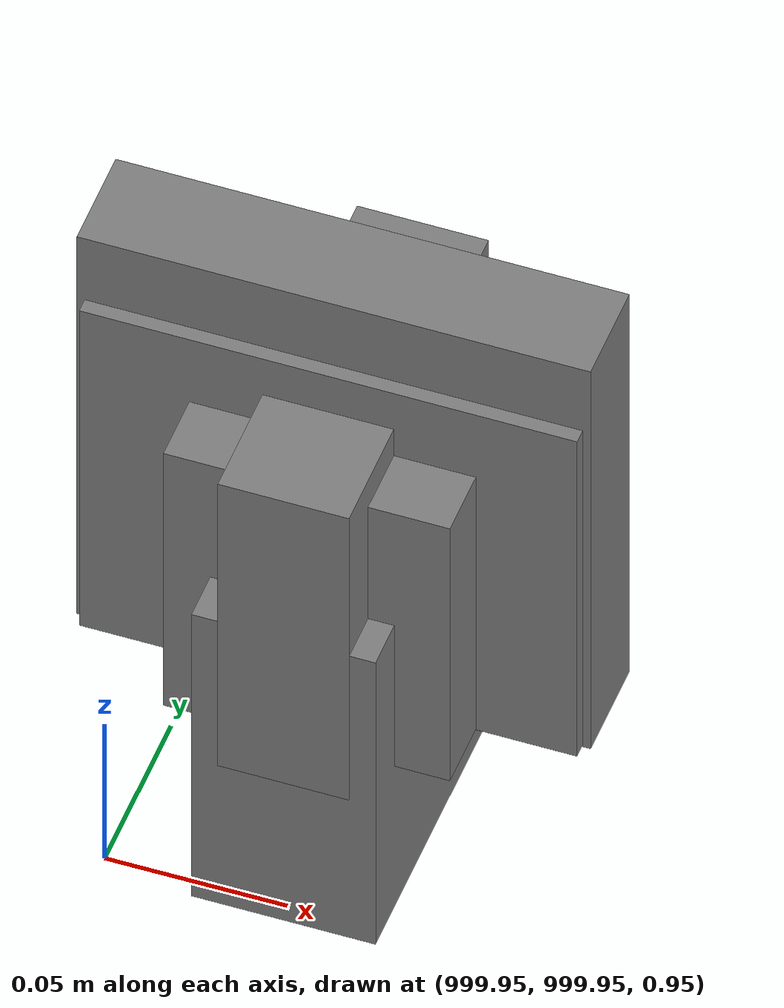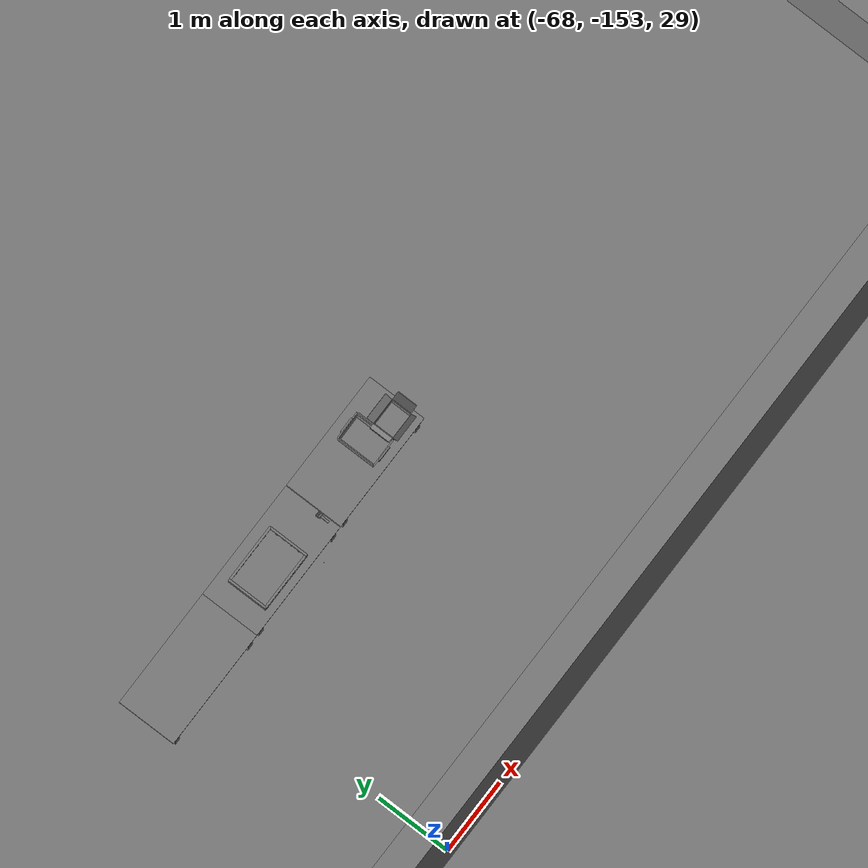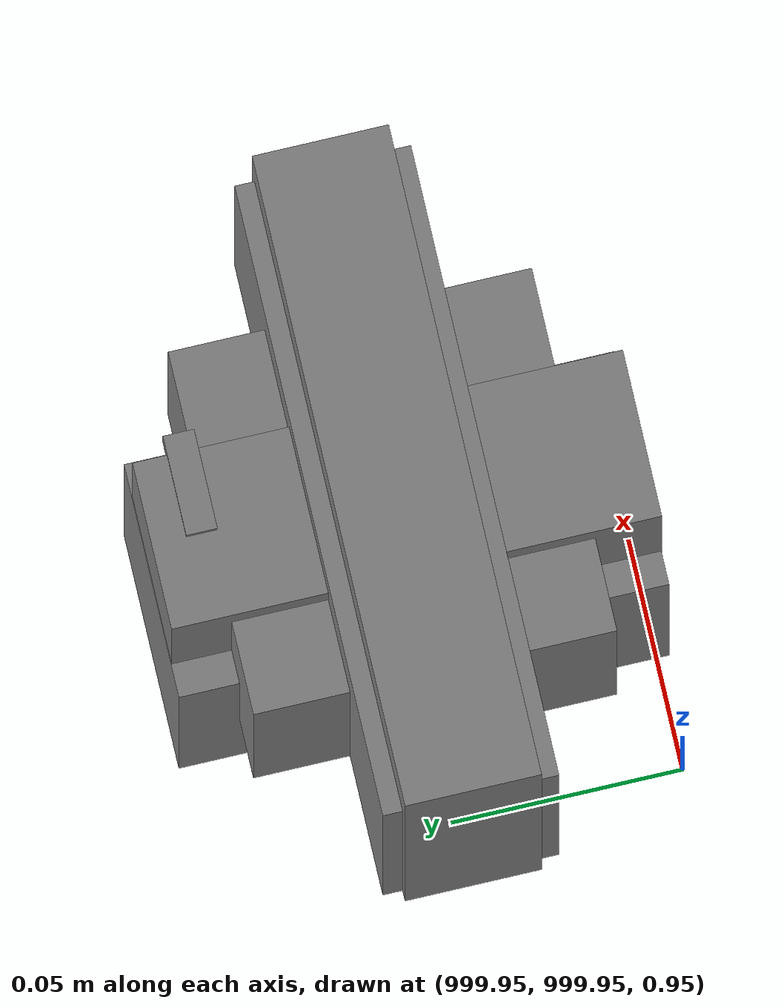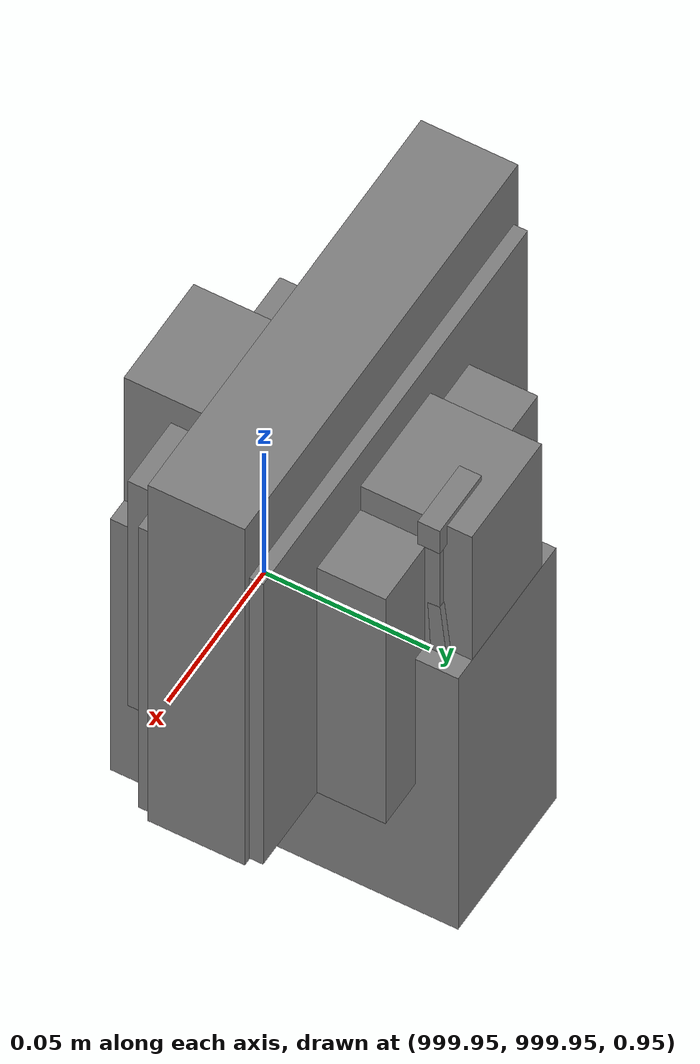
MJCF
<mujoco>
    <option gravity="0.000000000 0.000000000 -9.810000420" timestep="0.0049999999" integrator="implicitfast" density="1.225" viscosity="1.8000001e-05" noslip_iterations="10" iterations="100" sdf_iterations="50">
        <flag multiccd="disable"/>
    </option>
    <size memory="1000M"/>
    <compiler coordinate="local"/>
    <worldbody>
        <light cutoff="30" pos="0 1 1" dir="0 -1 -2"/>
        <light cutoff="30" pos="0 -1 1" dir="0 1 -2"/>
        <body pos="-66.301406860 -149.729705811 31.168004990" euler="94.557899475 71.999000549 90.222785950" mocap="true" name="spotlight2_SpotLight"/>
        <body pos="1000.000000000 1000.000000000 1.000000000" euler="0.000011953 0.000005123 -179.999984741" name="openloong_gripper_2f85_fix_base_usda_intel_box">
            <geom contype="1" conaffinity="1" density="1000" type="box" material="" rgba="0.500000000 0.500000000 0.500000000 1.000000000" solimp="0.899999976 0.949999988 0.001000000" friction="1.000000000 0.005000000 0.000100000" solref="0.020000000 1.000000000" margin="0" condim="3" group="0" pos="0.000000000 -0.000067139 0.000082284" quat="0.707106709 0.000000225 0.000000253 0.707106650" size="0.052800003 0.025300000 0.052800003" name="openloong_gripper_2f85_fix_base_usda_geom_2B3376B3_087E_48C5_8D4C_1C047C759649"/>
            <freejoint name="openloong_gripper_2f85_fix_base_usda_intel_box_joint"/>
            <site size="0.005000000 0.005000000 0.005000000" rgba="0.500000000 0.500000000 0.500000000 1.000000000" pos="0.000000000 0.000000000 0.000000000" quat="0.999961913 0.008726500 0.000000000 0.000000000" group="0" type="sphere" name="openloong_gripper_2f85_fix_base_usda_intel_boxsite"/>
        </body>
        <body pos="1000.000000000 999.999938965 1.000000000" euler="0.000000000 0.000000000 180.000000000" name="openloong_gripper_2f85_fix_base_usda_intelcore_i5">
            <geom contype="1" conaffinity="1" density="1000" type="box" material="" rgba="0.500000000 0.500000000 0.500000000 1.000000000" solimp="0.899999976 0.949999988 0.001000000" friction="1.000000000 0.005000000 0.000100000" solref="0.020000000 1.000000000" margin="0" condim="3" group="0" pos="0.000000000 0.000000000 0.051722717" quat="0.707106709 0.000000000 0.000000000 -0.707106769" size="0.052800000 0.018080002 0.052800000" name="openloong_gripper_2f85_fix_base_usda_geom_26764003_FC02_4BC9_BF18_E2B69BBDA964"/>
            <freejoint name="openloong_gripper_2f85_fix_base_usda_intelcore_i5_joint"/>
            <site size="0.005000000 0.005000000 0.005000000" rgba="0.500000000 0.500000000 0.500000000 1.000000000" pos="0.000000000 0.000000000 0.000000000" quat="0.999961913 0.008726534 0.000000000 0.000000000" group="0" type="sphere" name="openloong_gripper_2f85_fix_base_usda_intelcore_i5site"/>
        </body>
        <body pos="1000.000000000 1000.000000000 1.000000000" euler="0.000000000 0.000000000 180.000000000" name="openloong_gripper_2f85_fix_base_usda_wifi_box">
            <geom contype="1" conaffinity="1" density="1000" type="box" material="" rgba="0.500000000 0.500000000 0.500000000 1.000000000" solimp="0.899999976 0.949999988 0.001000000" friction="1.000000000 0.005000000 0.000100000" solref="0.020000000 1.000000000" margin="0" condim="3" group="0" pos="0.000000000 0.000000000 0.058978677" quat="0.000000000 0.000000047 0.000000000 1.000000000" size="0.068499997 0.018999999 0.059000000" name="openloong_gripper_2f85_fix_base_usda_geom_2B17B4CB_CAF9_428E_98D7_DFDB49278465"/>
            <freejoint name="openloong_gripper_2f85_fix_base_usda_wifi_box_joint"/>
            <site size="0.005000000 0.005000000 0.005000000" rgba="0.500000000 0.500000000 0.500000000 1.000000000" pos="0.000000000 0.000000000 0.000000000" quat="0.999961913 0.008726500 0.000000000 0.000000000" group="0" type="sphere" name="openloong_gripper_2f85_fix_base_usda_wifi_boxsite"/>
        </body>
        <body pos="1000.000000000 1000.000000000 1.000000000" euler="0.000000000 0.000000000 180.000000000" name="openloong_gripper_2f85_fix_base_usda_cpu_fan">
            <geom contype="1" conaffinity="1" density="1000" type="box" material="" rgba="0.500000000 0.500000000 0.500000000 1.000000000" solimp="0.899999976 0.949999988 0.001000000" friction="1.000000000 0.005000000 0.000100000" solref="0.020000000 1.000000000" margin="0" condim="3" group="0" pos="0.000000000 0.000000000 0.070034981" quat="0.000000000 0.000000000 0.000000000 1.000000000" size="0.070700005 0.014699999 0.070700005" name="openloong_gripper_2f85_fix_base_usda_geom_116A40E6_BF6A_4EC8_B5BE_8A7D9540B2CD"/>
            <freejoint name="openloong_gripper_2f85_fix_base_usda_cpu_fan_joint"/>
            <site size="0.005000000 0.005000000 0.005000000" rgba="0.500000000 0.500000000 0.500000000 1.000000000" pos="0.000000000 0.000000000 0.000000000" quat="0.999961913 0.008726535 0.000000000 0.000000000" group="0" type="sphere" name="openloong_gripper_2f85_fix_base_usda_cpu_fancsite"/>
        </body>
        <body pos="-65.950508118 -149.096893311 31.168724060" euler="-52.188762665 29.440589905 150.760543823" mocap="true" name="spotlight3_SpotLight"/>
        <body pos="1000.000000000 1000.000000000 1.000000000" euler="0.000000000 0.000000000 180.000000000" name="openloong_gripper_2f85_fix_base_usda_battery_01">
            <geom contype="1" conaffinity="1" density="1000" type="box" material="" rgba="0.500000000 0.500000000 0.500000000 1.000000000" solimp="0.899999976 0.949999988 0.001000000" friction="1.000000000 0.005000000 0.000100000" solref="0.020000000 1.000000000" margin="0" condim="3" group="0" pos="-0.011123657 -0.041940309 0.101691343" quat="1.000000000 0.000000000 0.000000000 0.000000000" size="0.010800000 0.003375000 0.004725000" name="openloong_gripper_2f85_fix_base_usda_geom_7681F90B_C849_4CA1_9E6F_ED62C9002A8B"/>
            <geom contype="1" conaffinity="1" density="1000" type="box" material="" rgba="0.500000000 0.500000000 0.500000000 1.000000000" solimp="0.899999976 0.949999988 0.001000000" friction="1.000000000 0.005000000 0.000100000" solref="0.020000000 1.000000000" margin="0" condim="3" group="0" pos="-0.010876465 -0.044247437 0.047066893" quat="0.998702705 -0.050920475 0.000000000 0.000000000" size="0.009450001 0.002700000 0.024975000" name="openloong_gripper_2f85_fix_base_usda_geom_0D5D2AD3_1249_449C_BDE7_3FE39321A59F"/>
            <geom contype="1" conaffinity="1" density="1000" type="box" material="" rgba="0.500000000 0.500000000 0.500000000 1.000000000" solimp="0.899999976 0.949999988 0.001000000" friction="1.000000000 0.005000000 0.000100000" solref="0.020000000 1.000000000" margin="0" condim="3" group="0" pos="-0.001235962 -0.000659180 0.047381196" quat="1.000000000 0.000000000 0.000000000 0.000000000" size="0.039420001 0.039150000 0.047250003" name="openloong_gripper_2f85_fix_base_usda_geom_4A98105F_F2EF_4161_8DDD_5F3AD24D1150"/>
            <geom contype="1" conaffinity="1" density="1000" type="box" material="" rgba="0.500000000 0.500000000 0.500000000 1.000000000" solimp="0.899999976 0.949999988 0.001000000" friction="1.000000000 0.005000000 0.000100000" solref="0.020000000 1.000000000" margin="0" condim="3" group="0" pos="-0.010876465 -0.039138794 0.009851727" quat="1.000000000 0.000000000 0.000000000 0.000000000" size="0.009450001 0.010800000 0.013500000" name="openloong_gripper_2f85_fix_base_usda_geom_1F7BD837_D580_44A5_8DD1_7070A9677272"/>
            <geom contype="1" conaffinity="1" density="1000" type="box" material="" rgba="0.500000000 0.500000000 0.500000000 1.000000000" solimp="0.899999976 0.949999988 0.001000000" friction="1.000000000 0.005000000 0.000100000" solref="0.020000000 1.000000000" margin="0" condim="3" group="0" pos="-0.010876465 -0.041528322 0.071508206" quat="1.000000000 0.000000000 0.000000000 0.000000000" size="0.009450001 0.002700000 0.027000001" name="openloong_gripper_2f85_fix_base_usda_geom_5DBB67C1_CDD8_423C_90B5_08C79D7E55B0"/>
            <freejoint name="openloong_gripper_2f85_fix_base_usda_battery_01_joint"/>
            <site size="0.005000000 0.005000000 0.005000000" rgba="0.500000000 0.500000000 0.500000000 1.000000000" pos="0.000000000 0.000000000 0.000000000" quat="0.999961913 0.008726500 0.000000000 0.000000000" group="0" type="sphere" name="openloong_gripper_2f85_fix_base_usda_battery_01site"/>
        </body>
        <body pos="-66.351821899 -149.275619507 31.164560318" euler="-0.121234640 -18.244626999 99.922203064" mocap="true" name="spotlight4_SpotLight"/>
        <body pos="-64.866622925 -149.383972168 30.183746338" euler="89.999984741 89.999946594 0.000000000" name="openloong_gripper_2f85_fix_base_usda_bluebox_01">
            <geom contype="1" conaffinity="1" density="1000" type="box" material="" rgba="0.500000000 0.500000000 0.500000000 1.000000000" solimp="0.899999976 0.949999988 0.001000000" friction="1.000000000 0.005000000 0.000100000" solref="0.020000000 1.000000000" margin="0" condim="3" group="0" pos="0.276580811 0.187225342 0.000068665" quat="0.707106948 0.000077471 0.707106352 0.000077486" size="0.100000001 0.057999998 0.010000000" name="openloong_gripper_2f85_fix_base_usda_geom_38D414F5_2BA8_46CE_B094_B999188A6CF7"/>
            <geom contype="1" conaffinity="1" density="1000" type="box" material="" rgba="0.500000000 0.500000000 0.500000000 1.000000000" solimp="0.899999976 0.949999988 0.001000000" friction="1.000000000 0.005000000 0.000100000" solref="0.020000000 1.000000000" margin="0" condim="3" group="0" pos="0.000000000 0.002883911 0.000000000" quat="0.999999881 0.000000000 0.000000000 0.000000000" size="0.254000008 0.003000000 0.172000006" name="openloong_gripper_2f85_fix_base_usda_geom_052E5537_D0CC_45B1_81FA_08120B495C94"/>
            <geom contype="1" conaffinity="1" density="1000" type="box" material="" rgba="0.500000000 0.500000000 0.500000000 1.000000000" solimp="0.899999976 0.949999988 0.001000000" friction="1.000000000 0.005000000 0.000100000" solref="0.020000000 1.000000000" margin="0" condim="3" group="0" pos="0.000000000 0.124874115 0.173484802" quat="0.999796331 0.020176515 -0.000000015 0.000000030" size="0.259999990 0.119999997 0.007000000" name="openloong_gripper_2f85_fix_base_usda_geom_603AB8FC_05E0_452E_9B6A_A41E7E2AC8DB"/>
            <geom contype="1" conaffinity="1" density="1000" type="box" material="" rgba="0.500000000 0.500000000 0.500000000 1.000000000" solimp="0.899999976 0.949999988 0.001000000" friction="1.000000000 0.005000000 0.000100000" solref="0.020000000 1.000000000" margin="0" condim="3" group="0" pos="0.000000000 0.124874115 -0.173469543" quat="0.999796331 -0.020176545 -0.000000015 0.000000000" size="0.259999990 0.119999997 0.007000000" name="openloong_gripper_2f85_fix_base_usda_geom_2A784937_6D66_483E_BE51_CB3F4585F0F5"/>
            <geom contype="1" conaffinity="1" density="1000" type="box" material="" rgba="0.500000000 0.500000000 0.500000000 1.000000000" solimp="0.899999976 0.949999988 0.001000000" friction="1.000000000 0.005000000 0.000100000" solref="0.020000000 1.000000000" margin="0" condim="3" group="0" pos="0.000000000 0.214008331 0.188980103" quat="0.999912977 0.013176724 0.000000015 0.000000000" size="0.259999990 0.029999999 0.012500000" name="openloong_gripper_2f85_fix_base_usda_geom_58CB3F16_96C1_4754_AE79_CF6F9DBDFE05"/>
            <geom contype="1" conaffinity="1" density="1000" type="box" material="" rgba="0.500000000 0.500000000 0.500000000 1.000000000" solimp="0.899999976 0.949999988 0.001000000" friction="1.000000000 0.005000000 0.000100000" solref="0.020000000 1.000000000" margin="0" condim="3" group="0" pos="-0.258361816 0.125289917 0.001876831" quat="0.702796936 -0.020792112 0.710783124 0.020769298" size="0.189999998 0.119999997 0.009000000" name="openloong_gripper_2f85_fix_base_usda_geom_AFF06BF0_5FB4_4C52_992B_61674EA4195E"/>
            <geom contype="1" conaffinity="1" density="1000" type="box" material="" rgba="0.500000000 0.500000000 0.500000000 1.000000000" solimp="0.899999976 0.949999988 0.001000000" friction="1.000000000 0.005000000 0.000100000" solref="0.020000000 1.000000000" margin="0" condim="3" group="0" pos="0.000000000 0.214008331 -0.188980103" quat="0.999912977 -0.013176769 0.000000030 0.000000015" size="0.259999990 0.029999999 0.012500000" name="openloong_gripper_2f85_fix_base_usda_geom_FB00186C_77C6_4229_96C0_4E6D04A7F143"/>
            <geom contype="1" conaffinity="1" density="1000" type="box" material="" rgba="0.500000000 0.500000000 0.500000000 1.000000000" solimp="0.899999976 0.949999988 0.001000000" friction="1.000000000 0.005000000 0.000100000" solref="0.020000000 1.000000000" margin="0" condim="3" group="0" pos="-0.276611328 0.187225342 0.000068665" quat="0.707106650 0.000077441 0.707106709 0.000077456" size="0.100000001 0.057999998 0.010000000" name="openloong_gripper_2f85_fix_base_usda_geom_5BD511F2_DF96_4EFE_B69E_6E405E7A6562"/>
            <geom contype="1" conaffinity="1" density="1000" type="box" material="" rgba="0.500000000 0.500000000 0.500000000 1.000000000" solimp="0.899999976 0.949999988 0.001000000" friction="1.000000000 0.005000000 0.000100000" solref="0.020000000 1.000000000" margin="0" condim="3" group="0" pos="0.258331299 0.125289917 0.001876831" quat="0.702851415 0.018856421 0.710823774 -0.019329369" size="0.189999998 0.119999997 0.009000000" name="openloong_gripper_2f85_fix_base_usda_geom_BB54A82E_7FFA_4905_8AA7_3CA97CB0F5A3"/>
            <freejoint name="openloong_gripper_2f85_fix_base_usda_bluebox_01_joint"/>
            <site size="0.005000000 0.005000000 0.005000000" rgba="0.500000000 0.500000000 0.500000000 1.000000000" pos="0.000000000 0.000000000 0.000000000" quat="0.999961913 0.008726534 0.000000000 0.000000000" group="0" type="sphere" name="openloong_gripper_2f85_fix_base_usda_bluebox_01site"/>
        </body>
        <body pos="-64.496299744 -149.491867065 30.235729218" euler="0.000000000 0.000000000 89.999946594" name="openloong_gripper_2f85_fix_base_usda_cardboardbox_01">
            <geom contype="1" conaffinity="1" density="1000" type="box" material="" rgba="0.500000000 0.500000000 0.500000000 1.000000000" solimp="0.899999976 0.949999988 0.001000000" friction="1.000000000 0.005000000 0.000100000" solref="0.020000000 1.000000000" margin="0" condim="3" group="0" pos="-0.003166199 -0.004086494 0.005052090" quat="1.000000000 0.000000000 0.000000000 0.000000000" size="0.142499998 0.177500010 0.005000000" name="openloong_gripper_2f85_fix_base_usda_geom_ECF6A40D_C9E0_4A0E_961A_642226C52873"/>
            <geom contype="1" conaffinity="1" density="1000" type="box" material="" rgba="0.500000000 0.500000000 0.500000000 1.000000000" solimp="0.899999976 0.949999988 0.001000000" friction="1.000000000 0.005000000 0.000100000" solref="0.020000000 1.000000000" margin="0" condim="3" group="0" pos="-0.003166199 0.170316696 0.150570869" quat="1.000000000 0.000000000 0.000000000 0.000000000" size="0.142499998 0.005000000 0.149999991" name="openloong_gripper_2f85_fix_base_usda_geom_D4FE6743_C093_4857_96D4_7B09B60865C4"/>
            <geom contype="1" conaffinity="1" density="1000" type="box" material="" rgba="0.500000000 0.500000000 0.500000000 1.000000000" solimp="0.899999976 0.949999988 0.001000000" friction="1.000000000 0.005000000 0.000100000" solref="0.020000000 1.000000000" margin="0" condim="3" group="0" pos="-0.147399902 -0.005307198 0.150570869" quat="1.000000000 0.000000000 0.000000000 0.000000000" size="0.005000000 0.177500010 0.149999991" name="openloong_gripper_2f85_fix_base_usda_geom_770C2655_437A_4873_9313_444E12F13BD7"/>
            <geom contype="1" conaffinity="1" density="1000" type="box" material="" rgba="0.500000000 0.500000000 0.500000000 1.000000000" solimp="0.899999976 0.949999988 0.001000000" friction="1.000000000 0.005000000 0.000100000" solref="0.020000000 1.000000000" margin="0" condim="3" group="0" pos="0.140275955 -0.005307198 0.150570869" quat="1.000000000 0.000000000 0.000000000 0.000000000" size="0.005000000 0.177500010 0.149999991" name="openloong_gripper_2f85_fix_base_usda_geom_ABFEE113_7EA0_4424_995F_8B5311BAAE31"/>
            <geom contype="1" conaffinity="1" density="1000" type="box" material="" rgba="0.500000000 0.500000000 0.500000000 1.000000000" solimp="0.899999976 0.949999988 0.001000000" friction="1.000000000 0.005000000 0.000100000" solref="0.020000000 1.000000000" margin="0" condim="3" group="0" pos="-0.003166199 -0.181550980 0.150570869" quat="1.000000000 0.000000000 0.000000000 0.000000000" size="0.142499998 0.005000000 0.149999991" name="openloong_gripper_2f85_fix_base_usda_geom_F2DA9A1A_3F2B_487E_9CDE_6582AF291DC7"/>
            <freejoint name="openloong_gripper_2f85_fix_base_usda_cardboardbox_01_joint"/>
            <site size="0.005000000 0.005000000 0.005000000" rgba="0.500000000 0.500000000 0.500000000 1.000000000" pos="0.000000000 0.000000000 0.000000000" quat="0.999961913 0.008726535 0.000000000 0.000000000" group="0" type="sphere" name="openloong_gripper_2f85_fix_base_usda_site_90D292E8_2E9F_4977_BC90_2D0B9C7B67D1"/>
            <body pos="0.139160156 -0.004048347 0.301930904" euler="-179.999954224 49.383502960 179.999954224" name="openloong_gripper_2f85_fix_base_usda_A1_006">
                <geom contype="1" conaffinity="1" density="1000" type="box" material="" rgba="0.500000000 0.500000000 0.500000000 1.000000000" solimp="0.899999976 0.949999988 0.001000000" friction="1.000000000 0.005000000 0.000100000" solref="0.020000000 1.000000000" margin="0" condim="3" group="0" pos="-0.071587563 0.000009537 0.001745224" quat="0.999999881 0.000000000 0.000000000 0.000000000" size="0.071249999 0.179999992 0.002500000" name="openloong_gripper_2f85_fix_base_usda_geom_79BE74FF_59B7_4902_B52A_2F746FB6CDC6"/>
                <joint armature="0" stiffness="0.07" damping="0.0099999998" axis="0.000000 1.000000 0.000000" type="hinge" name="openloong_gripper_2f85_fix_base_usda_A1_006"/>
            </body>
            <body pos="-0.145902634 -0.004086494 0.301938057" euler="-180.000000000 -60.000011444 -180.000000000" name="openloong_gripper_2f85_fix_base_usda_A2_006">
                <geom contype="1" conaffinity="1" density="1000" type="box" material="" rgba="0.500000000 0.500000000 0.500000000 1.000000000" solimp="0.899999976 0.949999988 0.001000000" friction="1.000000000 0.005000000 0.000100000" solref="0.020000000 1.000000000" margin="0" condim="3" group="0" pos="0.071268082 0.000009537 0.002717972" quat="0.000002921 0.000000000 -0.000000030 0.999999881" size="0.071249999 0.179999992 0.002500000" name="openloong_gripper_2f85_fix_base_usda_geom_FCB99B03_7904_4EE1_BD6D_EE636AD67BF8"/>
                <joint armature="0" stiffness="0.07" damping="0.0099999998" axis="0.000000 1.000000 0.000000" type="hinge" name="openloong_gripper_2f85_fix_base_usda_A2_006"/>
            </body>
            <body pos="-0.003385544 0.175991058 0.301930904" euler="-125.858116150 -0.000004561 0.000002331" name="openloong_gripper_2f85_fix_base_usda_B2_006">
                <geom contype="1" conaffinity="1" density="1000" type="box" material="" rgba="0.500000000 0.500000000 0.500000000 1.000000000" solimp="0.899999976 0.949999988 0.001000000" friction="1.000000000 0.005000000 0.000100000" solref="0.020000000 1.000000000" margin="0" condim="3" group="0" pos="0.000009537 -0.070939064 -0.002470016" quat="0.999614120 0.027776197 -0.000000015 0.000000030" size="0.137500003 0.064999998 0.005000000" name="openloong_gripper_2f85_fix_base_usda_geom_7648C9CC_5179_45F0_96E9_82F567EAF8DB"/>
                <joint armature="0" stiffness="0.07" damping="0.0099999998" axis="1.000000 0.000000 0.000000" type="hinge" name="openloong_gripper_2f85_fix_base_usda_B2_006"/>
            </body>
            <body pos="-0.003385544 -0.184140205 0.301938057" euler="147.805557251 0.000000000 0.000000000" name="openloong_gripper_2f85_fix_base_usda_B1_006">
                <geom contype="1" conaffinity="1" density="1000" type="box" material="" rgba="0.500000000 0.500000000 0.500000000 1.000000000" solimp="0.899999976 0.949999988 0.001000000" friction="1.000000000 0.005000000 0.000100000" solref="0.020000000 1.000000000" margin="0" condim="3" group="0" pos="-0.000028610 0.070202351 -0.002703667" quat="0.999614179 -0.027776167 0.000000000 0.000000000" size="0.137500003 0.064999998 0.005000000" name="openloong_gripper_2f85_fix_base_usda_geom_96078D7D_4227_40E9_ADCE_EC0EE90DCEF1"/>
                <joint armature="0" stiffness="0.07" damping="0.0099999998" axis="1.000000 0.000000 0.000000" type="hinge" name="openloong_gripper_2f85_fix_base_usda_B1_006"/>
            </body>
        </body>
        <body pos="-65.882858276 -149.481979370 30.229999542" euler="-64.487716675 0.000000000 0.000000000" name="openloong_gripper_2f85_fix_base_usda_Barcode">
            <geom contype="1" conaffinity="1" density="1000" type="box" material="" rgba="0.500000000 0.500000000 0.500000000 1.000000000" solimp="0.899999976 0.949999988 0.001000000" friction="1.000000000 0.005000000 0.000100000" solref="0.020000000 1.000000000" margin="0" condim="3" group="0" pos="0.000000000 0.013038635 0.001419067" quat="0.000000000 0.000000000 0.000000000 1.000000119" size="0.034000002 0.010000000 0.017999999" name="openloong_gripper_2f85_fix_base_usda_geom_1D29790E_AB16_4B48_AB4C_4048F33DEFA0"/>
            <geom contype="1" conaffinity="1" density="1000" type="box" material="" rgba="0.500000000 0.500000000 0.500000000 1.000000000" solimp="0.899999976 0.949999988 0.001000000" friction="1.000000000 0.005000000 0.000100000" solref="0.020000000 1.000000000" margin="0" condim="3" group="0" pos="0.000000000 -0.035301208 -0.007095337" quat="0.000000000 0.000000000 -0.043619365 0.999048233" size="0.028999999 0.010000000 0.020000000" name="openloong_gripper_2f85_fix_base_usda_geom_2800EE27_CB5E_47A1_B030_7F6282FC5AE2"/>
            <geom contype="1" conaffinity="1" density="1000" type="box" material="" rgba="0.500000000 0.500000000 0.500000000 1.000000000" solimp="0.899999976 0.949999988 0.001000000" friction="1.000000000 0.005000000 0.000100000" solref="0.020000000 1.000000000" margin="0" condim="3" group="0" pos="0.000000000 -0.043411255 -0.011749268" quat="0.922262907 0.386563420 0.000000000 0.000000000" size="0.026000001 0.010000000 0.020000000" name="openloong_gripper_2f85_fix_base_usda_geom_69ADA219_B4BB_4E8F_B3BC_166E7003E6F5"/>
            <geom contype="1" conaffinity="1" density="1000" type="box" material="" rgba="0.500000000 0.500000000 0.500000000 1.000000000" solimp="0.899999976 0.949999988 0.001000000" friction="1.000000000 0.005000000 0.000100000" solref="0.020000000 1.000000000" margin="0" condim="3" group="0" pos="0.000000000 -0.016967773 -0.031860352" quat="0.000000000 0.000000000 0.000000000 1.000000119" size="0.008000000 0.010000000 0.013000000" name="openloong_gripper_2f85_fix_base_usda_geom_8BA9FDAC_3551_49FB_8D72_A43921300F1D"/>
            <geom contype="1" conaffinity="1" density="1000" type="box" material="" rgba="0.500000000 0.500000000 0.500000000 1.000000000" solimp="0.899999976 0.949999988 0.001000000" friction="1.000000000 0.005000000 0.000100000" solref="0.020000000 1.000000000" margin="0" condim="3" group="0" pos="0.000000000 -0.001869202 0.000312805" quat="0.953716993 0.300705761 0.000000000 0.000000000" size="0.032000002 0.010000000 0.018999999" name="openloong_gripper_2f85_fix_base_usda_geom_AC27F9D0_3FDD_4CF9_B0F8_E060145BC679"/>
            <geom contype="1" conaffinity="1" density="1000" type="box" material="" rgba="0.500000000 0.500000000 0.500000000 1.000000000" solimp="0.899999976 0.949999988 0.001000000" friction="1.000000000 0.005000000 0.000100000" solref="0.020000000 1.000000000" margin="0" condim="3" group="0" pos="0.000000000 -0.019531250 -0.003173828" quat="0.953716993 0.300705761 0.000000000 0.000000000" size="0.030999999 0.010000000 0.020000000" name="openloong_gripper_2f85_fix_base_usda_geom_440A1747_2887_4688_8BE9_039488AE54C1"/>
            <geom contype="1" conaffinity="1" density="1000" type="box" material="" rgba="0.500000000 0.500000000 0.500000000 1.000000000" solimp="0.899999976 0.949999988 0.001000000" friction="1.000000000 0.005000000 0.000100000" solref="0.020000000 1.000000000" margin="0" condim="3" group="0" pos="0.000000000 -0.035301208 -0.007095337" quat="0.953716993 0.300705761 0.000000000 0.000000000" size="0.028999999 0.010000000 0.020000000" name="openloong_gripper_2f85_fix_base_usda_geom_31EA2CE7_EF8B_4F83_A363_C98AA785180B"/>
            <geom contype="1" conaffinity="1" density="1000" type="box" material="" rgba="0.500000000 0.500000000 0.500000000 1.000000000" solimp="0.899999976 0.949999988 0.001000000" friction="1.000000000 0.005000000 0.000100000" solref="0.020000000 1.000000000" margin="0" condim="3" group="0" pos="0.000000000 -0.042617798 -0.071121216" quat="0.000000000 0.000000000 0.000000000 1.000000119" size="0.013000000 0.021000000 0.059999999" name="openloong_gripper_2f85_fix_base_usda_geom_AD77B6E8_DD62_4FB8_A3E6_6B0A89AE8D10"/>
            <freejoint name="openloong_gripper_2f85_fix_base_usda_Barcode_joint"/>
            <site size="0.005000000 0.005000000 0.005000000" rgba="0.500000000 0.500000000 0.500000000 1.000000000" pos="0.000000000 0.000000000 0.000000000" quat="1.000000000 0.000000000 0.000000000 0.000000000" group="0" type="sphere" name="openloong_gripper_2f85_fix_base_usda_Barcode_site"/>
        </body>
        <body pos="-66.745018005 -149.392349243 30.184000015" euler="0.000000000 0.000000000 89.999946594" name="[22331720285228]_Basket_01">
            <geom contype="1" conaffinity="1" density="1000" type="box" material="" rgba="0.500000000 0.500000000 0.500000000 1.000000000" solimp="0.899999976 0.949999988 0.001000000" friction="1.000000000 0.005000000 0.000100000" solref="0.020000000 1.000000000" margin="0" condim="3" group="0" pos="-0.052425385 0.389207840 0.089787483" quat="0.707107008 0.000000000 0.000000000 0.707106411" size="0.014249999 0.014249999 0.059999999" name="[22331720285228]_geom_899AA583_B93C_45EC_9681_E8D28B4ED2A5"/>
            <geom contype="1" conaffinity="1" density="1000" type="box" material="" rgba="0.500000000 0.500000000 0.500000000 1.000000000" solimp="0.899999976 0.949999988 0.001000000" friction="1.000000000 0.005000000 0.000100000" solref="0.020000000 1.000000000" margin="0" condim="3" group="0" pos="0.264015198 -0.133043289 0.089787483" quat="0.707107008 0.000000000 0.000000000 0.707106411" size="0.014249999 0.014249999 0.059999999" name="[22331720285228]_geom_F4673B3F_3FD5_4AA6_B50A_298865C5EBC4"/>
            <geom contype="1" conaffinity="1" density="1000" type="box" material="" rgba="0.500000000 0.500000000 0.500000000 1.000000000" solimp="0.899999976 0.949999988 0.001000000" friction="1.000000000 0.005000000 0.000100000" solref="0.020000000 1.000000000" margin="0" condim="3" group="0" pos="-0.264015198 -0.265548706 0.089793205" quat="0.707107008 0.000000000 0.000000000 0.707106411" size="0.014249999 0.014249999 0.059999999" name="[22331720285228]_geom_BDAEE06D_F304_4A0A_B25C_32ADB248141F"/>
            <geom contype="1" conaffinity="1" density="1000" type="box" material="" rgba="0.500000000 0.500000000 0.500000000 1.000000000" solimp="0.899999976 0.949999988 0.001000000" friction="1.000000000 0.005000000 0.000100000" solref="0.020000000 1.000000000" margin="0" condim="3" group="0" pos="-0.160263062 -0.389322281 0.089793205" quat="0.707107008 0.000000000 0.000000000 0.707106411" size="0.014249999 0.014249999 0.059999999" name="[22331720285228]_geom_8B899B72_612C_48F7_9EEF_F5A68C82F937"/>
            <geom contype="1" conaffinity="1" density="1000" type="box" material="" rgba="0.500000000 0.500000000 0.500000000 1.000000000" solimp="0.899999976 0.949999988 0.001000000" friction="1.000000000 0.005000000 0.000100000" solref="0.020000000 1.000000000" margin="0" condim="3" group="0" pos="0.162265778 -0.389322281 0.089787483" quat="0.707107008 0.000000000 0.000000000 0.707106411" size="0.014249999 0.014249999 0.059999999" name="[22331720285228]_geom_5CE7E6C0_885A_4580_8F67_3BA456680D20"/>
            <geom contype="1" conaffinity="1" density="1000" type="box" material="" rgba="0.500000000 0.500000000 0.500000000 1.000000000" solimp="0.899999976 0.949999988 0.001000000" friction="1.000000000 0.005000000 0.000100000" solref="0.020000000 1.000000000" margin="0" condim="3" group="0" pos="0.264015198 0.389207840 0.089787483" quat="0.707107008 0.000000000 0.000000000 0.707106411" size="0.014249999 0.014249999 0.059999999" name="[22331720285228]_geom_EC7560F2_9B2B_4CA4_B4CB_4318E8BB5674"/>
            <geom contype="1" conaffinity="1" density="1000" type="box" material="" rgba="0.500000000 0.500000000 0.500000000 1.000000000" solimp="0.899999976 0.949999988 0.001000000" friction="1.000000000 0.005000000 0.000100000" solref="0.020000000 1.000000000" margin="0" condim="3" group="0" pos="-0.264015198 -0.133043289 0.089793205" quat="0.707107008 0.000000000 0.000000000 0.707106411" size="0.014249999 0.014249999 0.059999999" name="[22331720285228]_geom_6B66DB8E_E8A2_4AFF_AB59_348D3131F8B5"/>
            <geom contype="1" conaffinity="1" density="1000" type="box" material="" rgba="0.500000000 0.500000000 0.500000000 1.000000000" solimp="0.899999976 0.949999988 0.001000000" friction="1.000000000 0.005000000 0.000100000" solref="0.020000000 1.000000000" margin="0" condim="3" group="0" pos="-0.264026642 0.269256592 0.089793205" quat="0.707107008 0.000000000 0.000000000 0.707106411" size="0.014249999 0.014249999 0.059999999" name="[22331720285228]_geom_721C2F8B_CCC3_4333_A1C5_108255FBFA30"/>
            <geom contype="1" conaffinity="1" density="1000" type="box" material="" rgba="0.500000000 0.500000000 0.500000000 1.000000000" solimp="0.899999976 0.949999988 0.001000000" friction="1.000000000 0.005000000 0.000100000" solref="0.020000000 1.000000000" margin="0" condim="3" group="0" pos="0.054462433 0.389207840 0.089787483" quat="0.707107008 0.000000000 0.000000000 0.707106411" size="0.014249999 0.014249999 0.059999999" name="[22331720285228]_geom_3DD4EB80_FCAE_4834_A3CD_020E11BE0948"/>
            <geom contype="1" conaffinity="1" density="1000" type="box" material="" rgba="0.500000000 0.500000000 0.500000000 1.000000000" solimp="0.899999976 0.949999988 0.001000000" friction="1.000000000 0.005000000 0.000100000" solref="0.020000000 1.000000000" margin="0" condim="3" group="0" pos="0.054462433 -0.389322281 0.089787483" quat="0.707107008 0.000000000 0.000000000 0.707106411" size="0.014249999 0.014249999 0.059999999" name="[22331720285228]_geom_80823D39_4039_4200_83E0_BFA0E4A99556"/>
            <geom contype="1" conaffinity="1" density="1000" type="box" material="" rgba="0.500000000 0.500000000 0.500000000 1.000000000" solimp="0.899999976 0.949999988 0.001000000" friction="1.000000000 0.005000000 0.000100000" solref="0.020000000 1.000000000" margin="0" condim="3" group="0" pos="0.264015198 0.269256592 0.089793205" quat="0.707107008 0.000000000 0.000000000 0.707106411" size="0.014249999 0.014249999 0.059999999" name="[22331720285228]_geom_792FFA72_4713_488E_9C5E_5530C92FFDBD"/>
            <geom contype="1" conaffinity="1" density="1000" type="box" material="" rgba="0.500000000 0.500000000 0.500000000 1.000000000" solimp="0.899999976 0.949999988 0.001000000" friction="1.000000000 0.005000000 0.000100000" solref="0.020000000 1.000000000" margin="0" condim="3" group="0" pos="0.264015198 -0.389322281 0.089787483" quat="0.707107008 0.000000000 0.000000000 0.707106411" size="0.014249999 0.014249999 0.059999999" name="[22331720285228]_geom_0090C7A9_95D5_418A_B553_19DD9C994952"/>
            <geom contype="1" conaffinity="1" density="1000" type="box" material="" rgba="0.500000000 0.500000000 0.500000000 1.000000000" solimp="0.899999976 0.949999988 0.001000000" friction="1.000000000 0.005000000 0.000100000" solref="0.020000000 1.000000000" margin="0" condim="3" group="0" pos="0.000000000 0.000000000 0.015998840" quat="0.707107008 0.000000000 0.000000000 0.707106411" size="0.403499991 0.279000014 0.015750000" name="[22331720285228]_geom_847555E6_2EA9_4009_A37D_B62502BCC47F"/>
            <geom contype="1" conaffinity="1" density="1000" type="box" material="" rgba="0.500000000 0.500000000 0.500000000 1.000000000" solimp="0.899999976 0.949999988 0.001000000" friction="1.000000000 0.005000000 0.000100000" solref="0.020000000 1.000000000" margin="0" condim="3" group="0" pos="0.000000000 -0.389476776 0.163619041" quat="0.707107008 0.000000000 0.000000000 0.707106411" size="0.015000000 0.277500004 0.015750000" name="[22331720285228]_geom_337AA051_2336_483F_9C04_01CAF0DF401F"/>
            <geom contype="1" conaffinity="1" density="1000" type="box" material="" rgba="0.500000000 0.500000000 0.500000000 1.000000000" solimp="0.899999976 0.949999988 0.001000000" friction="1.000000000 0.005000000 0.000100000" solref="0.020000000 1.000000000" margin="0" condim="3" group="0" pos="0.162265778 0.389207840 0.089787483" quat="0.707107008 0.000000000 0.000000000 0.707106411" size="0.014249999 0.014249999 0.059999999" name="[22331720285228]_geom_5E9BF7E4_7B7D_4B66_A538_5FC40A4E8E81"/>
            <geom contype="1" conaffinity="1" density="1000" type="box" material="" rgba="0.500000000 0.500000000 0.500000000 1.000000000" solimp="0.899999976 0.949999988 0.001000000" friction="1.000000000 0.005000000 0.000100000" solref="0.020000000 1.000000000" margin="0" condim="3" group="0" pos="0.000000000 0.389471054 0.163619041" quat="0.707107008 0.000000000 0.000000000 0.707106411" size="0.015000000 0.277500004 0.015750000" name="[22331720285228]_geom_BE0F9CC6_696B_4668_A520_019E704A36E6"/>
            <geom contype="1" conaffinity="1" density="1000" type="box" material="" rgba="0.500000000 0.500000000 0.500000000 1.000000000" solimp="0.899999976 0.949999988 0.001000000" friction="1.000000000 0.005000000 0.000100000" solref="0.020000000 1.000000000" margin="0" condim="3" group="0" pos="-0.263511658 0.000000000 0.163619041" quat="0.707107008 0.000000000 0.000000000 0.707106411" size="0.403499991 0.015000000 0.015750000" name="[22331720285228]_geom_851E9F80_33AD_4898_8359_F2E4C6AFA6C5"/>
            <geom contype="1" conaffinity="1" density="1000" type="box" material="" rgba="0.500000000 0.500000000 0.500000000 1.000000000" solimp="0.899999976 0.949999988 0.001000000" friction="1.000000000 0.005000000 0.000100000" solref="0.020000000 1.000000000" margin="0" condim="3" group="0" pos="-0.264015198 0.141334534 0.089793205" quat="0.707107008 0.000000000 0.000000000 0.707106411" size="0.014249999 0.014249999 0.059999999" name="[22331720285228]_geom_C604D658_9F19_44C2_84CE_D9477615B54E"/>
            <geom contype="1" conaffinity="1" density="1000" type="box" material="" rgba="0.500000000 0.500000000 0.500000000 1.000000000" solimp="0.899999976 0.949999988 0.001000000" friction="1.000000000 0.005000000 0.000100000" solref="0.020000000 1.000000000" margin="0" condim="3" group="0" pos="0.264015198 -0.265548706 0.089787483" quat="0.707107008 0.000000000 0.000000000 0.707106411" size="0.014249999 0.014249999 0.059999999" name="[22331720285228]_geom_33B1E980_3648_43EA_9CE3_C0211F2B39E1"/>
            <geom contype="1" conaffinity="1" density="1000" type="box" material="" rgba="0.500000000 0.500000000 0.500000000 1.000000000" solimp="0.899999976 0.949999988 0.001000000" friction="1.000000000 0.005000000 0.000100000" solref="0.020000000 1.000000000" margin="0" condim="3" group="0" pos="-0.160263062 0.389207840 0.089787483" quat="0.707107008 0.000000000 0.000000000 0.707106411" size="0.014249999 0.014249999 0.059999999" name="[22331720285228]_geom_3DAC4705_81A5_4CE5_8511_58B52B0630D1"/>
            <geom contype="1" conaffinity="1" density="1000" type="box" material="" rgba="0.500000000 0.500000000 0.500000000 1.000000000" solimp="0.899999976 0.949999988 0.001000000" friction="1.000000000 0.005000000 0.000100000" solref="0.020000000 1.000000000" margin="0" condim="3" group="0" pos="-0.052425385 -0.389322281 0.089787483" quat="0.707107008 0.000000000 0.000000000 0.707106411" size="0.014249999 0.014249999 0.059999999" name="[22331720285228]_geom_59E07D29_FF40_465B_B7E2_BEEC7D50B7F5"/>
            <geom contype="1" conaffinity="1" density="1000" type="box" material="" rgba="0.500000000 0.500000000 0.500000000 1.000000000" solimp="0.899999976 0.949999988 0.001000000" friction="1.000000000 0.005000000 0.000100000" solref="0.020000000 1.000000000" margin="0" condim="3" group="0" pos="-0.264026642 -0.389322281 0.089793205" quat="0.707107008 0.000000000 0.000000000 0.707106411" size="0.014249999 0.014249999 0.059999999" name="[22331720285228]_geom_F8AB94B0_EBF4_4C15_95D5_E991082444CE"/>
            <geom contype="1" conaffinity="1" density="1000" type="box" material="" rgba="0.500000000 0.500000000 0.500000000 1.000000000" solimp="0.899999976 0.949999988 0.001000000" friction="1.000000000 0.005000000 0.000100000" solref="0.020000000 1.000000000" margin="0" condim="3" group="0" pos="0.264015198 0.141334534 0.089787483" quat="0.707107008 0.000000000 0.000000000 0.707106411" size="0.014249999 0.014249999 0.059999999" name="[22331720285228]_geom_DB7F340F_418E_4E77_BFAD_04A2FFACD710"/>
            <geom contype="1" conaffinity="1" density="1000" type="box" material="" rgba="0.500000000 0.500000000 0.500000000 1.000000000" solimp="0.899999976 0.949999988 0.001000000" friction="1.000000000 0.005000000 0.000100000" solref="0.020000000 1.000000000" margin="0" condim="3" group="0" pos="-0.264015198 0.389207840 0.089793205" quat="0.707107008 0.000000000 0.000000000 0.707106411" size="0.014249999 0.014249999 0.059999999" name="[22331720285228]_geom_76E7C5D4_FD04_4CAC_9A87_452AAED02040"/>
            <geom contype="1" conaffinity="1" density="1000" type="box" material="" rgba="0.500000000 0.500000000 0.500000000 1.000000000" solimp="0.899999976 0.949999988 0.001000000" friction="1.000000000 0.005000000 0.000100000" solref="0.020000000 1.000000000" margin="0" condim="3" group="0" pos="0.264015198 0.004480362 0.089787483" quat="0.707107008 0.000000000 0.000000000 0.707106411" size="0.014249999 0.014249999 0.059999999" name="[22331720285228]_geom_FEF56E90_D8BA_4409_9B17_842B51310799"/>
            <geom contype="1" conaffinity="1" density="1000" type="box" material="" rgba="0.500000000 0.500000000 0.500000000 1.000000000" solimp="0.899999976 0.949999988 0.001000000" friction="1.000000000 0.005000000 0.000100000" solref="0.020000000 1.000000000" margin="0" condim="3" group="0" pos="0.263694763 -0.000011444 0.163619041" quat="0.707107008 0.000000000 0.000000000 0.707106411" size="0.403499991 0.015000000 0.015750000" name="[22331720285228]_geom_CC12B430_93DE_4416_822E_0D3A24C0FA3B"/>
            <geom contype="1" conaffinity="1" density="1000" type="box" material="" rgba="0.500000000 0.500000000 0.500000000 1.000000000" solimp="0.899999976 0.949999988 0.001000000" friction="1.000000000 0.005000000 0.000100000" solref="0.020000000 1.000000000" margin="0" condim="3" group="0" pos="-0.264015198 0.004480362 0.089793205" quat="0.707107008 0.000000000 0.000000000 0.707106411" size="0.014249999 0.014249999 0.059999999" name="[22331720285228]_geom_F5D48BDB_EF13_4482_8578_52E169211FC0"/>
            <freejoint name="[22331720285228]_joint_ECDA5ABA_B883_4FC0_B98E_0C5B9E12FBB5"/>
        </body>
        <body pos="0.000000000 0.000000000 0.000000000" euler="0.000000000 0.000000000 0.000000000" name="Static Objects_Static Objects">
            <geom contype="1" conaffinity="1" density="1000" type="box" material="" rgba="0.500000000 0.500000000 0.500000000 1.000000000" solimp="0.899999976 0.949999988 0.001000000" friction="1.000000000 0.005000000 0.000100000" solref="0.020000000 1.000000000" margin="0" condim="3" group="0" pos="-67.544113159 -149.365814209 29.727830887" quat="0.500000417 0.499999970 0.499999553 0.499999970" size="0.381000012 0.319999993 0.041000001" name="Static Objects_geom_06930242_DCE4_4547_8E3A_901CF0765452"/>
            <geom contype="1" conaffinity="1" density="1000" type="box" material="" rgba="0.500000000 0.500000000 0.500000000 1.000000000" solimp="0.899999976 0.949999988 0.001000000" friction="1.000000000 0.005000000 0.000100000" solref="0.020000000 1.000000000" margin="0" condim="3" group="0" pos="-68.239501953 -149.365814209 30.086868286" quat="0.500000417 0.499999970 0.499999553 0.499999970" size="0.370999992 0.039500002 0.745000005" name="Static Objects_geom_7974D5F7_831E_41FC_97DD_D5639A7276D6"/>
            <geom contype="1" conaffinity="1" density="1000" type="box" material="" rgba="0.500000000 0.500000000 0.500000000 1.000000000" solimp="0.899999976 0.949999988 0.001000000" friction="1.000000000 0.005000000 0.000100000" solref="0.020000000 1.000000000" margin="0" condim="3" group="0" pos="-68.239501953 -149.365814209 30.147235870" quat="0.500000417 0.499999970 0.499999553 0.499999970" size="0.400000006 0.022000000 0.800000012" name="Static Objects_geom_7262277C_7559_4D09_A985_9DCB7905F689"/>
            <geom contype="1" conaffinity="1" density="1000" type="box" material="" rgba="0.500000000 0.500000000 0.500000000 1.000000000" solimp="0.899999976 0.949999988 0.001000000" friction="1.000000000 0.005000000 0.000100000" solref="0.020000000 1.000000000" margin="0" condim="3" group="0" pos="-68.934890747 -149.365814209 29.727830887" quat="0.500000417 0.499999970 0.499999553 0.499999970" size="0.381000012 0.319999993 0.041000001" name="Static Objects_geom_80CB9D21_DF4F_40FE_88E1_31B441078326"/>
            <geom contype="1" conaffinity="1" density="1000" type="box" material="" rgba="0.500000000 0.500000000 0.500000000 1.000000000" solimp="0.899999976 0.949999988 0.001000000" friction="1.000000000 0.005000000 0.000100000" solref="0.020000000 1.000000000" margin="0" condim="3" group="0" pos="-68.239501953 -149.365814209 29.561563492" quat="0.500000417 0.499999970 0.499999553 0.499999970" size="0.020000000 0.022000000 0.660000026" name="Static Objects_geom_5811E938_B332_4125_AAD4_4138D91EEC2A"/>
            <geom contype="1" conaffinity="1" density="1000" type="box" material="" rgba="0.500000000 0.500000000 0.500000000 1.000000000" solimp="0.899999976 0.949999988 0.001000000" friction="1.000000000 0.005000000 0.000100000" solref="0.020000000 1.000000000" margin="0" condim="3" group="0" pos="-65.945671082 -149.365814209 29.727830887" quat="0.500000417 0.499999970 0.499999553 0.499999970" size="0.381000012 0.319999993 0.041000001" name="Static Objects_geom_060BEA15_A63F_4DF1_8945_EA76E639DF39"/>
            <geom contype="1" conaffinity="1" density="1000" type="box" material="" rgba="0.500000000 0.500000000 0.500000000 1.000000000" solimp="0.899999976 0.949999988 0.001000000" friction="1.000000000 0.005000000 0.000100000" solref="0.020000000 1.000000000" margin="0" condim="3" group="0" pos="-66.641059875 -149.365814209 30.086868286" quat="0.500000417 0.499999970 0.499999553 0.499999970" size="0.370999992 0.039500002 0.745000005" name="Static Objects_geom_6234560F_D7ED_40A3_B2A4_7371E9C026CE"/>
            <geom contype="1" conaffinity="1" density="1000" type="box" material="" rgba="0.500000000 0.500000000 0.500000000 1.000000000" solimp="0.899999976 0.949999988 0.001000000" friction="1.000000000 0.005000000 0.000100000" solref="0.020000000 1.000000000" margin="0" condim="3" group="0" pos="-66.641059875 -149.365814209 30.147235870" quat="0.500000417 0.499999970 0.499999553 0.499999970" size="0.400000006 0.022000000 0.800000012" name="Static Objects_geom_767CB5BA_3A58_4CFB_86BB_B4BE733830CA"/>
            <geom contype="1" conaffinity="1" density="1000" type="box" material="" rgba="0.500000000 0.500000000 0.500000000 1.000000000" solimp="0.899999976 0.949999988 0.001000000" friction="1.000000000 0.005000000 0.000100000" solref="0.020000000 1.000000000" margin="0" condim="3" group="0" pos="-67.336448669 -149.365814209 29.727830887" quat="0.500000417 0.499999970 0.499999553 0.499999970" size="0.381000012 0.319999993 0.041000001" name="Static Objects_geom_C63AA80B_BE12_42C0_B9CB_247298589A97"/>
            <geom contype="1" conaffinity="1" density="1000" type="box" material="" rgba="0.500000000 0.500000000 0.500000000 1.000000000" solimp="0.899999976 0.949999988 0.001000000" friction="1.000000000 0.005000000 0.000100000" solref="0.020000000 1.000000000" margin="0" condim="3" group="0" pos="-66.641059875 -149.365814209 29.561563492" quat="0.500000417 0.499999970 0.499999553 0.499999970" size="0.020000000 0.022000000 0.660000026" name="Static Objects_geom_F9E67F97_A0FB_4867_A815_B8EA44C669A1"/>
            <geom contype="1" conaffinity="1" density="1000" type="box" material="" rgba="0.500000000 0.500000000 0.500000000 1.000000000" solimp="0.899999976 0.949999988 0.001000000" friction="1.000000000 0.005000000 0.000100000" solref="0.020000000 1.000000000" margin="0" condim="3" group="0" pos="-64.338577271 -149.365814209 29.727830887" quat="0.500000417 0.499999970 0.499999553 0.499999970" size="0.381000012 0.319999993 0.041000001" name="Static Objects_geom_A37090B8_5181_4205_BBC8_1465EB2E7595"/>
            <geom contype="1" conaffinity="1" density="1000" type="box" material="" rgba="0.500000000 0.500000000 0.500000000 1.000000000" solimp="0.899999976 0.949999988 0.001000000" friction="1.000000000 0.005000000 0.000100000" solref="0.020000000 1.000000000" margin="0" condim="3" group="0" pos="-65.033966064 -149.365814209 30.086868286" quat="0.500000417 0.499999970 0.499999553 0.499999970" size="0.370999992 0.039500002 0.745000005" name="Static Objects_geom_F8ABB2A4_5552_4947_9189_D509179D5809"/>
            <geom contype="1" conaffinity="1" density="1000" type="box" material="" rgba="0.500000000 0.500000000 0.500000000 1.000000000" solimp="0.899999976 0.949999988 0.001000000" friction="1.000000000 0.005000000 0.000100000" solref="0.020000000 1.000000000" margin="0" condim="3" group="0" pos="-65.033966064 -149.365814209 30.147235870" quat="0.500000417 0.499999970 0.499999553 0.499999970" size="0.400000006 0.022000000 0.800000012" name="Static Objects_geom_CAC2A665_09E7_4BBC_9F27_4F31B8D76F8F"/>
            <geom contype="1" conaffinity="1" density="1000" type="box" material="" rgba="0.500000000 0.500000000 0.500000000 1.000000000" solimp="0.899999976 0.949999988 0.001000000" friction="1.000000000 0.005000000 0.000100000" solref="0.020000000 1.000000000" margin="0" condim="3" group="0" pos="-65.729354858 -149.365814209 29.727830887" quat="0.500000417 0.499999970 0.499999553 0.499999970" size="0.381000012 0.319999993 0.041000001" name="Static Objects_geom_B3E3FD48_5B79_44E0_BB27_D7AC9D332334"/>
            <geom contype="1" conaffinity="1" density="1000" type="box" material="" rgba="0.500000000 0.500000000 0.500000000 1.000000000" solimp="0.899999976 0.949999988 0.001000000" friction="1.000000000 0.005000000 0.000100000" solref="0.020000000 1.000000000" margin="0" condim="3" group="0" pos="-65.033966064 -149.365814209 29.561563492" quat="0.500000417 0.499999970 0.499999553 0.499999970" size="0.020000000 0.022000000 0.660000026" name="Static Objects_geom_347020F2_869F_4359_A05D_44B558691772"/>
            <geom contype="1" conaffinity="1" density="1000" type="box" material="" rgba="0.500000000 0.500000000 0.500000000 1.000000000" solimp="0.899999976 0.949999988 0.001000000" friction="1.000000000 0.005000000 0.000100000" solref="0.020000000 1.000000000" margin="0" condim="3" group="0" pos="-61.754566193 -137.853729248 33.906845093" quat="0.707107067 0.000000000 0.000000000 0.707106471" size="0.759999990 0.759999990 4.500000000" name="Static Objects_geom_A131A154_39F7_4B58_9EDE_13DCABB9F2A3"/>
            <geom contype="1" conaffinity="1" density="1000" type="box" material="" rgba="0.500000000 0.500000000 0.500000000 1.000000000" solimp="0.899999976 0.949999988 0.001000000" friction="1.000000000 0.005000000 0.000100000" solref="0.020000000 1.000000000" margin="0" condim="3" group="0" pos="-57.511135101 -144.927108765 31.707921982" quat="1.000000000 0.000000000 0.000000000 0.000000000" size="0.200000003 8.000000000 2.299999952" name="Static Objects_geom_F545B479_F85B_4C3F_88A4_5FA5DFABB83D"/>
            <geom contype="1" conaffinity="1" density="1000" type="box" material="" rgba="0.500000000 0.500000000 0.500000000 1.000000000" solimp="0.899999976 0.949999988 0.001000000" friction="1.000000000 0.005000000 0.000100000" solref="0.020000000 1.000000000" margin="0" condim="3" group="0" pos="-80.517646790 -157.574050903 31.688196182" quat="0.707107067 0.000000000 0.000000000 0.707106471" size="0.600000024 0.600000024 2.299999952" name="Static Objects_geom_A302024E_EACA_40AA_9F88_5AEC1B14FA86"/>
            <geom contype="1" conaffinity="1" density="1000" type="box" material="" rgba="0.500000000 0.500000000 0.500000000 1.000000000" solimp="0.899999976 0.949999988 0.001000000" friction="1.000000000 0.005000000 0.000100000" solref="0.020000000 1.000000000" margin="0" condim="3" group="0" pos="-80.711044312 -147.414932251 31.666158676" quat="1.000000000 0.000000000 0.000000000 0.000000000" size="0.200000003 10.000000000 2.299999952" name="Static Objects_geom_B7B54BF1_0BDE_48BC_BE33_9F5FE3662C8C"/>
            <geom contype="1" conaffinity="1" density="1000" type="box" material="" rgba="0.500000000 0.500000000 0.500000000 1.000000000" solimp="0.899999976 0.949999988 0.001000000" friction="1.000000000 0.005000000 0.000100000" solref="0.020000000 1.000000000" margin="0" condim="3" group="0" pos="-57.687217712 -137.434692383 31.688196182" quat="0.707107067 0.000000000 0.000000000 0.707106471" size="0.600000024 0.600000024 2.299999952" name="Static Objects_geom_0BD90F4A_BF97_434B_A9E0_7DE272974D68"/>
            <geom contype="1" conaffinity="1" density="1000" type="box" material="" rgba="0.500000000 0.500000000 0.500000000 1.000000000" solimp="0.899999976 0.949999988 0.001000000" friction="1.000000000 0.005000000 0.000100000" solref="0.020000000 1.000000000" margin="0" condim="3" group="0" pos="-69.537033081 -140.263229370 31.714921951" quat="0.707107067 0.000000000 0.000000000 0.707106471" size="0.759999990 4.500000000 2.299999952" name="Static Objects_geom_54FA4C54_14E2_4027_920B_E5C12A219E73"/>
            <geom contype="1" conaffinity="1" density="1000" type="box" material="" rgba="0.500000000 0.500000000 0.500000000 1.000000000" solimp="0.899999976 0.949999988 0.001000000" friction="1.000000000 0.005000000 0.000100000" solref="0.020000000 1.000000000" margin="0" condim="3" group="0" pos="-80.073638916 -137.853713989 33.906845093" quat="0.707107067 0.000000000 0.000000000 0.707106471" size="0.759999990 0.759999990 4.500000000" name="Static Objects_geom_AA13CC80_8F75_4C73_8B24_1649B843D0A9"/>
            <geom contype="1" conaffinity="1" density="1000" type="box" material="" rgba="0.500000000 0.500000000 0.500000000 1.000000000" solimp="0.899999976 0.949999988 0.001000000" friction="1.000000000 0.005000000 0.000100000" solref="0.020000000 1.000000000" margin="0" condim="3" group="0" pos="-73.406707764 -155.734664917 31.707921982" quat="1.000000000 0.000000000 0.000000000 0.000000000" size="0.200000003 3.000000000 2.299999952" name="Static Objects_geom_71E33B6F_62D6_4D6D_9A38_461C33B2158F"/>
            <geom contype="1" conaffinity="1" density="1000" type="box" material="" rgba="0.500000000 0.500000000 0.500000000 1.000000000" solimp="0.899999976 0.949999988 0.001000000" friction="1.000000000 0.005000000 0.000100000" solref="0.020000000 1.000000000" margin="0" condim="3" group="0" pos="-68.497543335 -137.448257446 31.707921982" quat="0.707107067 0.000000000 0.000000000 0.707106471" size="0.200000003 14.000000000 2.299999952" name="Static Objects_geom_75E13D51_3CA9_4D02_B311_5F356528AA99"/>
            <geom contype="1" conaffinity="1" density="1000" type="cylinder" material="" rgba="0.500000000 0.500000000 0.500000000 1.000000000" solimp="0.899999976 0.949999988 0.001000000" friction="1.000000000 0.005000000 0.000100000" solref="0.020000000 1.000000000" margin="0" condim="3" group="0" pos="-68.868522644 -142.134506226 31.711090088" quat="0.707107067 0.000000000 0.000000000 0.707106471" size="0.509999990 2.299999952 1.000000000" name="Static Objects_geom_C862D9B5_4EEF_4FFD_BDC8_697E46637B8E"/>
            <geom contype="1" conaffinity="1" density="1000" type="plane" material="" rgba="0.500000000 0.500000000 0.500000000 1.000000000" solimp="0.899999976 0.949999988 0.001000000" friction="1.000000000 0.005000000 0.000100000" solref="0.020000000 1.000000000" margin="0" condim="3" group="0" pos="-72.873703003 -147.131927490 29.409669876" quat="1.000000000 0.000000000 0.000000000 0.000000000" size="18.000000000 14.000000000 1.000000000" name="Static Objects_geom_FC088E23_816A_4E5D_AD2F_31ACF7726A2C"/>
            <geom contype="1" conaffinity="1" density="1000" type="box" material="" rgba="0.500000000 0.500000000 0.500000000 1.000000000" solimp="0.899999976 0.949999988 0.001000000" friction="1.000000000 0.005000000 0.000100000" solref="0.020000000 1.000000000" margin="0" condim="3" group="0" pos="-79.943580627 -157.782272339 31.707921982" quat="0.707107067 0.000000000 0.000000000 0.707106471" size="0.200000003 7.000000000 2.299999952" name="Static Objects_geom_DC68164B_40E1_4CD5_90E2_DBC6C12A9FBF"/>
            <geom contype="1" conaffinity="1" density="1000" type="box" material="" rgba="0.500000000 0.500000000 0.500000000 1.000000000" solimp="0.899999976 0.949999988 0.001000000" friction="1.000000000 0.005000000 0.000100000" solref="0.020000000 1.000000000" margin="0" condim="3" group="0" pos="-65.421028137 -152.903442383 31.707921982" quat="0.707107067 0.000000000 0.000000000 0.707106471" size="0.200000003 7.800000191 2.299999952" name="Static Objects_geom_680DD774_5431_4E87_BF95_4A2B0CB4FBB3"/>
            <geom contype="1" conaffinity="1" density="1000" type="box" material="" rgba="0.500000000 0.500000000 0.500000000 1.000000000" solimp="0.899999976 0.949999988 0.001000000" friction="1.000000000 0.005000000 0.000100000" solref="0.020000000 1.000000000" margin="0" condim="3" group="0" pos="-74.776908875 -149.964416504 31.688196182" quat="1.000000000 0.000000000 0.000000000 0.000000000" size="0.600000024 0.409999996 2.299999952" name="Static Objects_geom_948AB052_9B71_4985_9A64_15952C2322DA"/>
            <geom contype="1" conaffinity="1" density="1000" type="cylinder" material="" rgba="0.500000000 0.500000000 0.500000000 1.000000000" solimp="0.899999976 0.949999988 0.001000000" friction="1.000000000 0.005000000 0.000100000" solref="0.020000000 1.000000000" margin="0" condim="3" group="0" pos="-60.161884308 -142.134506226 31.711090088" quat="0.707107067 0.000000000 0.000000000 0.707106471" size="0.509999990 2.299999952 1.000000000" name="Static Objects_geom_1A9C4248_8885_4DCA_BD41_4070BF62E300"/>
            <geom contype="1" conaffinity="1" density="1000" type="cylinder" material="" rgba="0.500000000 0.500000000 0.500000000 1.000000000" solimp="0.899999976 0.949999988 0.001000000" friction="1.000000000 0.005000000 0.000100000" solref="0.020000000 1.000000000" margin="0" condim="3" group="0" pos="-75.382453918 -149.963455200 31.711090088" quat="0.707107067 0.000000000 0.000000000 0.707106471" size="0.409999996 2.299999952 1.000000000" name="Static Objects_geom_8A0303E7_2276_4481_9E54_887728AEA9FA"/>
            <geom contype="1" conaffinity="1" density="1000" type="cylinder" material="" rgba="0.500000000 0.500000000 0.500000000 1.000000000" solimp="0.899999976 0.949999988 0.001000000" friction="1.000000000 0.005000000 0.000100000" solref="0.020000000 1.000000000" margin="0" condim="3" group="0" pos="-74.154960632 -149.963455200 31.711090088" quat="0.707107067 0.000000000 0.000000000 0.707106471" size="0.409999996 2.299999952 1.000000000" name="Static Objects_geom_1EB6D509_9DD2_4834_B1FD_71F1000D09C8"/>
            <geom contype="1" conaffinity="1" density="1000" type="cylinder" material="" rgba="0.500000000 0.500000000 0.500000000 1.000000000" solimp="0.899999976 0.949999988 0.001000000" friction="1.000000000 0.005000000 0.000100000" solref="0.020000000 1.000000000" margin="0" condim="3" group="0" pos="-77.566612244 -142.134506226 31.711090088" quat="0.707107067 0.000000000 0.000000000 0.707106471" size="0.509999990 2.299999952 1.000000000" name="Static Objects_geom_B5B95E79_DCD3_418A_8BEC_B993D9A89B24"/>
        </body>
        <body pos="-66.291030884 -149.869689941 29.018842697" euler="0.000000000 0.000000000 89.999946594" mocap="true" name="openloong_gripper_2f85_fix_base_usda_leftHandMocap"/>
        <body pos="-66.291030884 -149.869689941 29.018842697" euler="0.000000000 0.000000000 89.999946594" mocap="true" name="openloong_gripper_2f85_fix_base_usda_rightHandMocap"/>
        <body pos="-66.291030884 -149.869689941 30.218843460" euler="0.000000000 0.000000000 89.999946594" name="openloong_gripper_2f85_fix_base_usda_base_link">
            <geom contype="1" conaffinity="1" density="1000" type="mesh" material="" rgba="0.783999979 0.783999979 0.783999979 1.000000000" solimp="0.899999976 0.949999988 0.001000000" friction="1.000000000 0.005000000 0.000100000" solref="0.020000000 1.000000000" margin="0" condim="3" group="3" mesh="base_link" pos="0.000000000 0.000000000 0.000000000" quat="1.000000000 0.000000000 0.000000000 0.000000000" size="1.000000000 1.000000000 1.000000000" name="openloong_gripper_2f85_fix_base_usda__geom_7_14CB3DAB_D683_4C00_945A_E4FA57B6B8D3"/>
            <site size="0.005000000 0.005000000 0.005000000" rgba="0.500000000 0.500000000 0.500000000 1.000000000" pos="0.000000000 0.000000000 0.000000000" quat="1.000000000 0.000000000 0.000000000 0.000000000" group="0" type="sphere" name="openloong_gripper_2f85_fix_base_usda_imu"/>
            <inertial mass="22.447001" pos="-0.005664100 -0.001336700 0.238289997" diaginertia="0.374352545 0.277180195 0.220617250" quat="0.999247074 0.035235517 -0.015086859 0.006023135"/>
            <body pos="0.000000000 0.000000000 0.299997330" euler="0.000000000 0.000000000 0.000000000" name="openloong_gripper_2f85_fix_base_usda_dummy_body">
                <geom contype="1" conaffinity="1" density="1000" type="sphere" material="" rgba="0.783999979 0.783999979 0.783999979 1.000000000" solimp="0.899999976 0.949999988 0.001000000" friction="1.000000000 0.005000000 0.000100000" solref="0.020000000 1.000000000" margin="0" condim="3" group="3" pos="0.000000000 0.000000000 0.000000000" quat="1.000000000 0.000000000 0.000000000 0.000000000" size="0.010000000 0.000000000 0.000000000" name="openloong_gripper_2f85_fix_base_usda__geom_8_EA9A3C40_7200_40B0_A91C_B3C40FE37F03"/>
                <joint armature="0.0099999998" stiffness="0" damping="0.1" axis="0.000000 0.000000 1.000000" type="hinge" name="openloong_gripper_2f85_fix_base_usda_dummy_joint"/>
                <site size="0.010000000 0.005000000 0.005000000" rgba="0.500000000 0.500000000 0.500000000 1.000000000" pos="0.000000000 0.000000000 0.000000000" quat="1.000000000 0.000000000 0.000000000 0.000000000" group="3" type="sphere" name="openloong_gripper_2f85_fix_base_usda_dummy_site"/>
            </body>
            <body pos="0.009002686 0.000000000 0.406400681" euler="0.000000000 0.000000000 0.000000000" name="openloong_gripper_2f85_fix_base_usda_Link_head_yaw">
                <geom contype="1" conaffinity="1" density="1000" type="mesh" material="" rgba="0.783999979 0.783999979 0.783999979 1.000000000" solimp="0.899999976 0.949999988 0.001000000" friction="1.000000000 0.005000000 0.000100000" solref="0.020000000 1.000000000" margin="0" condim="3" group="3" mesh="Link_head_yaw" pos="0.000000000 0.000000000 0.000000000" quat="1.000000000 0.000000000 0.000000000 0.000000000" size="1.000000000 1.000000000 1.000000000" name="openloong_gripper_2f85_fix_base_usda__geom_10_767E2CF1_2FEC_48A3_BAC5_6A24CD8B4AEE"/>
                <inertial mass="0.84249002" pos="0.000000000 -0.002081400 0.044801001" diaginertia="0.000700588 0.000629000 0.000553812" quat="0.706933022 -0.015675601 0.015677100 0.706933022"/>
                <body pos="0.000000000 -0.034599304 0.048500061" euler="0.000000000 0.000000000 0.000000000" name="openloong_gripper_2f85_fix_base_usda_Link_head_pitch">
                    <geom contype="1" conaffinity="1" density="1000" type="mesh" material="" rgba="0.783999979 0.783999979 0.783999979 1.000000000" solimp="0.899999976 0.949999988 0.001000000" friction="1.000000000 0.005000000 0.000100000" solref="0.020000000 1.000000000" margin="0" condim="3" group="3" mesh="Link_head_pitch" pos="0.000000000 0.000000000 0.000000000" quat="1.000000000 0.000000000 0.000000000 0.000000000" size="1.000000000 1.000000000 1.000000000" name="openloong_gripper_2f85_fix_base_usda__geom_12_51C94A6C_2993_457A_ADC6_92A41860E0F8"/>
                    <inertial mass="1.3943" pos="0.020569000 0.033004001 0.125000000" diaginertia="0.006381400 0.006289940 0.004481460" quat="0.973390222 0.008406822 0.228157058 0.019624906"/>
                    <body pos="0.000000000 0.029998779 0.000000000" euler="0.000000000 0.000000000 0.000000000" name="openloong_gripper_2f85_fix_base_usda_neck_center_body">
                        <site size="0.010000000 0.005000000 0.005000000" rgba="0.500000000 0.500000000 0.500000000 1.000000000" pos="0.000000000 0.000000000 0.000000000" quat="1.000000000 0.000000000 0.000000000 0.000000000" group="3" type="sphere" name="openloong_gripper_2f85_fix_base_usda_neck_center_site"/>
                        <body pos="0.020004272 0.000000000 0.149999619" euler="-0.000002229 39.998176575 -90.000205994" name="openloong_gripper_2f85_fix_base_usda_camera_head">
                            <site size="0.010000000 0.005000000 0.005000000" rgba="0.500000000 0.500000000 0.500000000 1.000000000" pos="0.000000000 0.000000000 0.000000000" quat="1.000000000 0.000000000 0.000000000 0.000000000" group="3" type="sphere" name="openloong_gripper_2f85_fix_base_usda_camera_head_site"/>
                        </body>
                    </body>
                </body>
            </body>
            <body pos="0.003997803 -0.161598206 0.392200470" euler="0.000000000 0.000000000 0.000000000" name="openloong_gripper_2f85_fix_base_usda_Link_arm_r_01">
                <geom contype="1" conaffinity="1" density="1000" type="mesh" material="" rgba="0.783999979 0.783999979 0.783999979 1.000000000" solimp="0.899999976 0.949999988 0.001000000" friction="1.000000000 0.005000000 0.000100000" solref="0.020000000 1.000000000" margin="0" condim="3" group="3" mesh="Link_arm_r_01" pos="0.000000000 0.000000000 0.000000000" quat="1.000000000 0.000000000 0.000000000 0.000000000" size="1.000000000 1.000000000 1.000000000" name="openloong_gripper_2f85_fix_base_usda__geom_14_3AFCE8A3_1183_4CDE_9F40_611B8405554E"/>
                <joint armature="0.0099999998" stiffness="0" damping="1" axis="0.000000 -1.000000 0.000000" limited="true" range="-170.000015259 170.000015259" type="hinge" name="openloong_gripper_2f85_fix_base_usda_J_arm_r_01"/>
                <inertial mass="0.75641" pos="0.004494600 -0.038293999 -0.000001874" diaginertia="0.000842990 0.000803050 0.000587120" quat="-0.000163502 0.707098067 0.000812463 0.707115054"/>
                <body pos="-0.041992188 -0.041000366 0.000000000" euler="0.000000000 0.000000000 0.000000000" name="openloong_gripper_2f85_fix_base_usda_Link_arm_r_02">
                    <geom contype="1" conaffinity="1" density="1000" type="mesh" material="" rgba="0.783999979 0.783999979 0.783999979 1.000000000" solimp="0.899999976 0.949999988 0.001000000" friction="1.000000000 0.005000000 0.000100000" solref="0.020000000 1.000000000" margin="0" condim="3" group="3" mesh="Link_arm_r_02" pos="0.000000000 0.000000000 0.000000000" quat="1.000000000 0.000000000 0.000000000 0.000000000" size="1.000000000 1.000000000 1.000000000" name="openloong_gripper_2f85_fix_base_usda__geom_16_120CF7A3_351B_4244_95C1_E9294C71BE42"/>
                    <joint armature="0.0099999998" stiffness="0" damping="1" axis="-1.000000 0.000000 0.000000" limited="true" range="-105.000244141 105.000244141" type="hinge" name="openloong_gripper_2f85_fix_base_usda_J_arm_r_02"/>
                    <inertial mass="0.98500001" pos="0.041999999 -0.067430697 0.000000000" diaginertia="0.002262690 0.001730990 0.001154020" quat="0.500000000 0.500000000 -0.500000000 0.500000000"/>
                    <body pos="0.041992188 -0.122596741 0.000000000" euler="0.000000000 0.000000000 0.000000000" name="openloong_gripper_2f85_fix_base_usda_Link_arm_r_03">
                        <geom contype="1" conaffinity="1" density="1000" type="mesh" material="" rgba="0.783999979 0.783999979 0.783999979 1.000000000" solimp="0.899999976 0.949999988 0.001000000" friction="1.000000000 0.005000000 0.000100000" solref="0.020000000 1.000000000" margin="0" condim="3" group="3" mesh="Link_arm_r_03" pos="0.000000000 0.000000000 0.000000000" quat="1.000000000 0.000000000 0.000000000 0.000000000" size="1.000000000 1.000000000 1.000000000" name="openloong_gripper_2f85_fix_base_usda__geom_18_69116ED5_76C0_414D_81C7_D17F23E6CD36"/>
                        <joint armature="0.0099999998" stiffness="0" damping="1" axis="0.000000 -1.000000 0.000000" limited="true" range="-170.000015259 170.000015259" type="hinge" name="openloong_gripper_2f85_fix_base_usda_J_arm_r_03"/>
                        <inertial mass="0.95899999" pos="-0.001413580 -0.164663002 0.020757901" diaginertia="0.002101340 0.002064590 0.000754802" quat="0.560480952 0.454391927 -0.443732947 0.531497955"/>
                        <body pos="0.035293579 -0.177406311 0.023998260" euler="0.000000000 0.000000000 0.000000000" name="openloong_gripper_2f85_fix_base_usda_Link_arm_r_04">
                            <geom contype="1" conaffinity="1" density="1000" type="mesh" material="" rgba="0.783999979 0.783999979 0.783999979 1.000000000" solimp="0.899999976 0.949999988 0.001000000" friction="1.000000000 0.005000000 0.000100000" solref="0.020000000 1.000000000" margin="0" condim="3" group="3" mesh="Link_arm_r_04" pos="0.000000000 0.000000000 0.000000000" quat="1.000000000 0.000000000 0.000000000 0.000000000" size="1.000000000 1.000000000 1.000000000" name="openloong_gripper_2f85_fix_base_usda__geom_20_44D04A24_5853_4662_8DFB_486537470828"/>
                            <joint armature="0.0099999998" stiffness="0" damping="1" axis="-1.000000 0.000000 0.000000" limited="true" range="0.000000000 170.000015259" type="hinge" name="openloong_gripper_2f85_fix_base_usda_J_arm_r_04"/>
                            <inertial mass="0.60000002" pos="-0.038727000 -0.060766999 -0.021003000" diaginertia="0.001092610 0.000712422 0.000645102" quat="0.327701002 0.632602990 -0.467366993 0.523443997"/>
                            <body pos="-0.035293579 -0.103492737 -0.023998260" euler="0.000000000 0.000000000 0.000000000" name="openloong_gripper_2f85_fix_base_usda_Link_arm_r_05">
                                <geom contype="1" conaffinity="1" density="1000" type="mesh" material="" rgba="0.783999979 0.783999979 0.783999979 1.000000000" solimp="0.899999976 0.949999988 0.001000000" friction="1.000000000 0.005000000 0.000100000" solref="0.020000000 1.000000000" margin="0" condim="3" group="3" mesh="Link_arm_r_05" pos="0.000000000 0.000000000 0.000000000" quat="1.000000000 0.000000000 0.000000000 0.000000000" size="1.000000000 1.000000000 1.000000000" name="openloong_gripper_2f85_fix_base_usda__geom_22_F5E42D6E_86C6_4632_BC30_2773ED50BADE"/>
                                <joint armature="0.0099999998" stiffness="0" damping="1" axis="0.000000 -1.000000 0.000000" limited="true" range="-170.000015259 170.000015259" type="hinge" name="openloong_gripper_2f85_fix_base_usda_J_arm_r_05"/>
                                <inertial mass="0.68976003" pos="0.000032712 -0.068658002 -0.000111780" diaginertia="0.002522510 0.002411100 0.000448695" quat="0.707660973 0.706543028 -0.002603360 0.002470550"/>
                                <body pos="-0.026489258 -0.196502686 0.000000000" euler="0.000000000 0.000000000 0.000000000" name="openloong_gripper_2f85_fix_base_usda_Link_arm_r_06">
                                    <geom contype="1" conaffinity="1" density="1000" type="mesh" material="" rgba="0.783999979 0.783999979 0.783999979 1.000000000" solimp="0.899999976 0.949999988 0.001000000" friction="1.000000000 0.005000000 0.000100000" solref="0.020000000 1.000000000" margin="0" condim="3" group="3" mesh="Link_arm_r_06" pos="0.000000000 0.000000000 0.000000000" quat="1.000000000 0.000000000 0.000000000 0.000000000" size="1.000000000 1.000000000 1.000000000" name="openloong_gripper_2f85_fix_base_usda__geom_24_A6B08345_219F_4CEC_B83B_F97581261B08"/>
                                    <joint armature="0.0099999998" stiffness="0" damping="1" axis="1.000000 0.000000 0.000000" limited="true" range="-105.000244141 105.000244141" type="hinge" name="openloong_gripper_2f85_fix_base_usda_J_arm_r_06"/>
                                    <inertial mass="0.28" pos="0.026078001 -0.000000896 0.001663700" diaginertia="0.000156930 0.000145601 0.000104979" quat="0.707080841 0.001851080 0.001883810 0.707127810"/>
                                    <body pos="0.026489258 0.000000000 0.031799316" euler="0.000000000 0.000000000 0.000000000" name="openloong_gripper_2f85_fix_base_usda_Link_arm_r_07">
                                        <geom contype="1" conaffinity="1" density="1000" type="mesh" material="" rgba="0.783999979 0.783999979 0.783999979 1.000000000" solimp="0.899999976 0.949999988 0.001000000" friction="1.000000000 0.005000000 0.000100000" solref="0.020000000 1.000000000" margin="0" condim="3" group="3" mesh="Link_arm_r_07" pos="0.000000000 0.000000000 0.000000000" quat="1.000000000 0.000000000 0.000000000 0.000000000" size="1.000000000 1.000000000 1.000000000" name="openloong_gripper_2f85_fix_base_usda__geom_26_14B44721_3F4C_4BEC_81AA_370A6C4D4BB1"/>
                                        <joint armature="0.0099999998" stiffness="0" damping="1" axis="0.000000 0.000000 1.000000" limited="true" range="-60.000133514 60.000133514" type="hinge" name="openloong_gripper_2f85_fix_base_usda_J_arm_r_07"/>
                                        <inertial mass="0.61353999" pos="-0.007859000 -0.158170000 -0.027736001" diaginertia="0.003037610 0.002570910 0.000729379" quat="0.427542925 0.443532884 -0.553093910 0.560867906"/>
                                        <body pos="0.000000000 0.286994934 -0.270000458" euler="150.000350952 -0.000001649 -0.000000442" name="openloong_gripper_2f85_fix_base_usda_camera_wrist_r">
                                            <site size="0.010000000 0.005000000 0.005000000" rgba="0.500000000 0.500000000 0.500000000 1.000000000" pos="0.000000000 0.000000000 0.000000000" quat="1.000000000 0.000000000 0.000000000 0.000000000" group="3" type="sphere" name="openloong_gripper_2f85_fix_base_usda_camera_wrist_r_site"/>
                                        </body>
                                        <body pos="0.000000000 -0.220008850 -0.033002853" euler="0.000000000 0.000000000 179.999969482" name="openloong_gripper_2f85_fix_base_usda_ee_center_body_r">
                                            <site size="0.010000000 0.005000000 0.005000000" rgba="0.500000000 0.500000000 0.500000000 1.000000000" pos="0.000000000 0.000000000 0.000000000" quat="1.000000000 0.000000000 0.000000000 0.000000000" group="3" type="sphere" name="openloong_gripper_2f85_fix_base_usda_ee_center_site_r"/>
                                        </body>
                                        <body pos="0.000000000 -0.066001892 -0.031000137" euler="89.999984741 0.000000000 180.000000000" name="openloong_gripper_2f85_fix_base_usda_zbr_base_link">
                                            <geom contype="1" conaffinity="1" density="1000" type="mesh" material="" rgba="0.783999979 0.783999979 0.783999979 1.000000000" solimp="0.899999976 0.949999988 0.001000000" friction="1.000000000 0.005000000 0.000100000" solref="0.020000000 1.000000000" margin="0" condim="3" group="3" mesh="base" pos="0.000000000 0.000003815 -0.000007629" quat="1.000000000 0.000000000 0.000000000 0.000000000" size="1.000000238 1.000000238 1.000000238" name="openloong_gripper_2f85_fix_base_usda__geom_30_16DFC6B9_83C4_450F_97CF_7BB80B657118"/>
                                            <inertial mass="0.77744102" pos="0.000000000 -0.000027039 0.035467502" diaginertia="0.000260285 0.000225381 0.000152708" quat="0.999998808 -0.001528488 0.000000000 0.000000000"/>
                                            <body pos="-0.030609138 0.004745484 0.065696731" euler="-89.999984741 -0.000000000 0.000000000" name="openloong_gripper_2f85_fix_base_usda_r_left_driver">
                                                <geom contype="1" conaffinity="1" density="1000" type="mesh" material="" rgba="0.783999979 0.783999979 0.783999979 1.000000000" solimp="0.899999976 0.949999988 0.001000000" friction="1.000000000 0.005000000 0.000100000" solref="0.020000000 1.000000000" margin="0" condim="3" group="3" mesh="driver" pos="0.030609138 0.054901138 -0.004699708" quat="0.707106829 0.707106709 0.000000000 -0.000000000" size="1.000000238 1.000000238 1.000000238" name="openloong_gripper_2f85_fix_base_usda__geom_32_2996E8AB_8A28_477A_AB3F_8FE69622D449"/>
                                                <joint armature="0.0049999999" stiffness="0" damping="0.1" axis="0.000000 0.000000 1.000000" limited="true" range="0.000000000 51.566200256" type="hinge" name="openloong_gripper_2f85_fix_base_usda_r_left_driver_joint"/>
                                                <inertial mass="0.0089956298" pos="0.000000000 0.017754700 0.001073140" diaginertia="0.000001724 0.000001609 0.000000322" quat="0.681301236 0.732003212 0.000000000 0.000000000"/>
                                                <body pos="-0.031402595 0.004524232 -0.010200503" euler="0.000000000 0.000000000 180.000000000" name="openloong_gripper_2f85_fix_base_usda_r_left_coupler">
                                                    <geom contype="1" conaffinity="1" density="1000" type="mesh" material="" rgba="0.783999979 0.783999979 0.783999979 1.000000000" solimp="0.899999976 0.949999988 0.001000000" friction="1.000000000 0.005000000 0.000100000" solref="0.020000000 1.000000000" margin="0" condim="3" group="3" mesh="coupler" pos="-0.062011734 -0.050354015 0.005500795" quat="0.707106829 -0.707106709 0.000000000 -0.000000000" size="1.000000238 1.000000238 1.000000238" name="openloong_gripper_2f85_fix_base_usda__geom_34_83B7FCFA_FFE6_442F_BCD1_D5C63C495BA0"/>
                                                    <inertial mass="0.0140974" pos="0.000000000 0.003012090 0.023217499" diaginertia="0.000004162 0.000003522 0.000000888" quat="0.705635548 -0.045590367 0.045590367 0.705635548"/>
                                                </body>
                                            </body>
                                            <body pos="-0.012695315 -0.012001040 0.072212234" euler="-89.999984741 -0.000000000 0.000000000" name="openloong_gripper_2f85_fix_base_usda_r_left_spring_link">
                                                <geom contype="1" conaffinity="1" density="1000" type="mesh" material="" rgba="0.783999979 0.783999979 0.783999979 1.000000000" solimp="0.899999976 0.949999988 0.001000000" friction="1.000000000 0.005000000 0.000100000" solref="0.020000000 1.000000000" margin="0" condim="3" group="3" mesh="spring_link" pos="0.012695315 0.061416641 0.012050631" quat="0.707106829 0.707106709 0.000000000 -0.000000000" size="1.000000238 1.000000238 1.000000238" name="openloong_gripper_2f85_fix_base_usda__geom_36_F6855798_8EBA_4E02_9AE3_171B46F79008"/>
                                                <joint armature="0.001" stiffness="0.050000001" damping="0.00125" axis="0.000000 0.000000 1.000000" limited="true" range="-17.000000000 51.566200256" type="hinge" name="openloong_gripper_2f85_fix_base_usda_r_left_spring_link_joint"/>
                                                <inertial mass="0.0221642" pos="-0.000000009 0.018162400 0.021265799" diaginertia="0.000008969 0.000006717 0.000002639" quat="0.663403213 -0.244737089 0.244737089 0.663403213"/>
                                                <body pos="-0.038208015 -0.042503368 0.002950669" euler="180.000000000 0.000000000 -0.002185660" name="openloong_gripper_2f85_fix_base_usda_r_left_follower">
                                                    <geom contype="1" conaffinity="1" density="1000" type="mesh" material="" rgba="0.783999979 0.783999979 0.783999979 1.000000000" solimp="0.899999976 0.949999988 0.001000000" friction="1.000000000 0.005000000 0.000100000" solref="0.020000000 1.000000000" margin="0" condim="3" group="3" mesh="tongue" pos="0.050918590 -0.103920005 -0.009099962" quat="0.707106829 -0.707106709 0.000000030 0.000000030" size="1.000000238 1.000000238 1.000000238" name="openloong_gripper_2f85_fix_base_usda__geom_40_2E211738_6D1A_4855_B8BF_AE3DAA5358E0"/>
                                                    <geom contype="1" conaffinity="1" density="1000" type="mesh" material="" rgba="0.783999979 0.783999979 0.783999979 1.000000000" solimp="0.899999976 0.949999988 0.001000000" friction="1.000000000 0.005000000 0.000100000" solref="0.020000000 1.000000000" margin="0" condim="3" group="3" mesh="follower" pos="0.050918590 -0.103920005 -0.009099962" quat="0.707106829 -0.707106709 0.000000030 0.000000030" size="1.000000238 1.000000238 1.000000238" name="openloong_gripper_2f85_fix_base_usda__geom_39_C6C3E525_ABEC_429F_8D5A_866DA219E7AD"/>
                                                    <joint armature="0.001" stiffness="0" damping="0.1" axis="0.000000 0.000000 1.000000" limited="true" range="-49.999961853 51.566200256" type="hinge" name="openloong_gripper_2f85_fix_base_usda_r_left_follower"/>
                                                    <inertial mass="0.0125222" pos="0.000000000 -0.011046000 0.012478600" diaginertia="0.000002674 0.000002456 0.000000602" quat="0.986436546 0.164143041 0.000000000 0.000000000"/>
                                                    <body pos="-0.037765510 -0.103912376 -0.009099962" euler="-89.999984741 0.000000000 0.000004829" name="openloong_gripper_2f85_fix_base_usda_r_left_pad">
                                                        <geom contype="1" conaffinity="1" density="1000" type="box" material="" rgba="0.550000012 0.550000012 0.550000012 1.000000000" solimp="0.949999988 0.990000010 0.001000000" friction="0.699999988 0.005000000 0.000100000" solref="0.020000000 1.000000000" margin="0" condim="3" group="3" mass="1e-06" pos="0.043243419 0.000003815 0.119995147" quat="0.999999881 0.000000000 0.000000000 0.000000000" size="0.002000001 0.011000003 0.009375002" name="openloong_gripper_2f85_fix_base_usda_r_left_pad1_F425C571_93FB_4A41_B133_4F82DA77EB55"/>
                                                        <geom contype="1" conaffinity="1" density="1000" type="box" material="" rgba="0.449999988 0.449999988 0.449999988 1.000000000" solimp="0.949999988 0.990000010 0.001000000" friction="0.600000024 0.005000000 0.000100000" solref="0.020000000 1.000000000" margin="0" condim="3" group="3" mass="1e-06" pos="0.043243419 0.000003815 0.138748199" quat="0.999999881 0.000000000 0.000000000 0.000000000" size="0.002000001 0.011000003 0.009375002" name="openloong_gripper_2f85_fix_base_usda_r_left_pad2_BB55EE72_98A1_411C_8E3B_AF07E5031A02"/>
                                                    </body>
                                                </body>
                                            </body>
                                            <body pos="0.030593880 -0.004753114 0.065696731" euler="89.999984741 0.000000000 180.000000000" name="openloong_gripper_2f85_fix_base_usda_r_right_driver">
                                                <geom contype="1" conaffinity="1" density="1000" type="mesh" material="" rgba="0.783999979 0.783999979 0.783999979 1.000000000" solimp="0.899999976 0.949999988 0.001000000" friction="1.000000000 0.005000000 0.000100000" solref="0.020000000 1.000000000" margin="0" condim="3" group="3" mesh="driver" pos="0.030593880 0.054901138 -0.004699708" quat="0.707106829 0.707106709 0.000000000 0.000000000" size="1.000000238 1.000000238 1.000000238" name="openloong_gripper_2f85_fix_base_usda__geom_42_0172B9EE_D703_4D5E_8D41_1A67960A09B3"/>
                                                <joint armature="0.0049999999" stiffness="0" damping="0.1" axis="0.000000 0.000000 1.000000" limited="true" range="0.000000000 51.566200256" type="hinge" name="openloong_gripper_2f85_fix_base_usda_r_right_driver_joint"/>
                                                <inertial mass="0.0089956298" pos="0.000000000 0.017754700 0.001073140" diaginertia="0.000001724 0.000001609 0.000000322" quat="0.681301236 0.732003212 0.000000000 0.000000000"/>
                                                <body pos="-0.031417854 0.004531861 -0.010202411" euler="0.000000000 0.000000000 180.000000000" name="openloong_gripper_2f85_fix_base_usda_r_right_coupler">
                                                    <geom contype="1" conaffinity="1" density="1000" type="mesh" material="" rgba="0.783999979 0.783999979 0.783999979 1.000000000" solimp="0.899999976 0.949999988 0.001000000" friction="1.000000000 0.005000000 0.000100000" solref="0.020000000 1.000000000" margin="0" condim="3" group="3" mesh="coupler" pos="-0.062042251 -0.050376903 0.005500795" quat="0.707106829 -0.707106709 0.000000000 0.000000000" size="1.000000238 1.000000238 1.000000238" name="openloong_gripper_2f85_fix_base_usda__geom_44_69187F0E_5807_4977_A5B7_052FFC908008"/>
                                                    <inertial mass="0.0140974" pos="0.000000000 0.003012090 0.023217499" diaginertia="0.000004162 0.000003522 0.000000888" quat="0.705635548 -0.045590367 0.045590367 0.705635548"/>
                                                </body>
                                            </body>
                                            <body pos="0.012695315 0.011997226 0.072219864" euler="89.999984741 0.000000000 180.000000000" name="openloong_gripper_2f85_fix_base_usda_r_right_spring_link">
                                                <geom contype="1" conaffinity="1" density="1000" type="mesh" material="" rgba="0.783999979 0.783999979 0.783999979 1.000000000" solimp="0.899999976 0.949999988 0.001000000" friction="1.000000000 0.005000000 0.000100000" solref="0.020000000 1.000000000" margin="0" condim="3" group="3" mesh="spring_link" pos="0.012695315 0.061424270 0.012048724" quat="0.707106829 0.707106709 0.000000000 0.000000000" size="1.000000238 1.000000238 1.000000238" name="openloong_gripper_2f85_fix_base_usda__geom_46_F575B098_3C7B_4C77_8814_AE2012D32163"/>
                                                <joint armature="0.001" stiffness="0.050000001" damping="0.00125" axis="0.000000 0.000000 1.000000" limited="true" range="-17.000000000 51.566200256" type="hinge" name="openloong_gripper_2f85_fix_base_usda_r_right_spring_link_joint"/>
                                                <inertial mass="0.0221642" pos="-0.000000009 0.018162400 0.021265799" diaginertia="0.000008969 0.000006717 0.000002639" quat="0.663403213 -0.244737089 0.244737089 0.663403213"/>
                                                <body pos="-0.038208015 -0.042495739 0.002950669" euler="180.000000000 0.000000000 0.000000000" name="openloong_gripper_2f85_fix_base_usda_r_right_follower">
                                                    <geom contype="1" conaffinity="1" density="1000" type="mesh" material="" rgba="0.783999979 0.783999979 0.783999979 1.000000000" solimp="0.899999976 0.949999988 0.001000000" friction="1.000000000 0.005000000 0.000100000" solref="0.020000000 1.000000000" margin="0" condim="3" group="3" mesh="follower" pos="0.050888073 -0.103927635 -0.009099962" quat="0.707106829 -0.707106709 0.000000000 0.000000000" size="1.000000238 1.000000238 1.000000238" name="openloong_gripper_2f85_fix_base_usda__geom_50_96DEEE74_5928_485A_A719_5DFBA14A238C"/>
                                                    <geom contype="1" conaffinity="1" density="1000" type="mesh" material="" rgba="0.783999979 0.783999979 0.783999979 1.000000000" solimp="0.899999976 0.949999988 0.001000000" friction="1.000000000 0.005000000 0.000100000" solref="0.020000000 1.000000000" margin="0" condim="3" group="3" mesh="tongue" pos="0.050888073 -0.103927635 -0.009099962" quat="0.707106829 -0.707106709 0.000000000 0.000000000" size="1.000000238 1.000000238 1.000000238" name="openloong_gripper_2f85_fix_base_usda__geom_49_F088D366_D98C_4F18_9B5E_3629465AD802"/>
                                                    <joint armature="0.001" stiffness="0" damping="0.1" axis="0.000000 0.000000 1.000000" limited="true" range="-49.999961853 51.566200256" type="hinge" name="openloong_gripper_2f85_fix_base_usda_r_right_follower_joint"/>
                                                    <inertial mass="0.0125222" pos="0.000000000 -0.011046000 0.012478600" diaginertia="0.000002674 0.000002456 0.000000602" quat="0.986436546 0.164143041 0.000000000 0.000000000"/>
                                                    <body pos="-0.037811287 -0.103927635 -0.009099962" euler="-89.999984741 0.000000000 0.000000000" name="openloong_gripper_2f85_fix_base_usda_r_right_pad">
                                                        <geom contype="1" conaffinity="1" density="1000" type="box" material="" rgba="0.449999988 0.449999988 0.449999988 1.000000000" solimp="0.949999988 0.990000010 0.001000000" friction="0.600000024 0.005000000 0.000100000" solref="0.020000000 1.000000000" margin="0" condim="3" group="3" mass="1e-06" pos="0.043258678 0.000000000 0.138748199" quat="1.000000000 0.000000000 0.000000000 0.000000000" size="0.002000001 0.011000003 0.009375002" name="openloong_gripper_2f85_fix_base_usda_r_right_pad2_DE84EC00_D583_4B88_886F_D36E1B544B92"/>
                                                        <geom contype="1" conaffinity="1" density="1000" type="box" material="" rgba="0.550000012 0.550000012 0.550000012 1.000000000" solimp="0.949999988 0.990000010 0.001000000" friction="0.699999988 0.005000000 0.000100000" solref="0.020000000 1.000000000" margin="0" condim="3" group="3" mass="1e-06" pos="0.043258678 0.000003815 0.120002776" quat="1.000000000 0.000000000 0.000000000 0.000000000" size="0.002000001 0.011000003 0.009375002" name="openloong_gripper_2f85_fix_base_usda_r_right_pad1_BA845DBF_A9B6_4C9E_97AC_EBD4D9A36064"/>
                                                    </body>
                                                </body>
                                            </body>
                                        </body>
                                    </body>
                                </body>
                            </body>
                        </body>
                    </body>
                </body>
            </body>
            <body pos="0.003997803 0.161590576 0.392200470" euler="0.000000000 0.000000000 0.000000000" name="openloong_gripper_2f85_fix_base_usda_Link_arm_l_01">
                <geom contype="1" conaffinity="1" density="1000" type="mesh" material="" rgba="0.783999979 0.783999979 0.783999979 1.000000000" solimp="0.899999976 0.949999988 0.001000000" friction="1.000000000 0.005000000 0.000100000" solref="0.020000000 1.000000000" margin="0" condim="3" group="3" mesh="Link_arm_l_01" pos="0.000000000 0.000000000 0.000000000" quat="1.000000000 0.000000000 0.000000000 0.000000000" size="1.000000000 1.000000000 1.000000000" name="openloong_gripper_2f85_fix_base_usda__geom_52_7B61429E_5BAF_4BB8_8CB3_2BCF2ADDEC6C"/>
                <joint armature="0.0099999998" stiffness="0" damping="1" axis="0.000000 1.000000 0.000000" limited="true" range="-170.000015259 170.000015259" type="hinge" name="openloong_gripper_2f85_fix_base_usda_J_arm_l_01"/>
                <inertial mass="0.75640601" pos="-0.004494650 0.038294200 -0.000001874" diaginertia="0.000842986 0.000803053 0.000587115" quat="-0.000812496 0.707115054 0.000163424 0.707098067"/>
                <body pos="0.042007446 0.041000366 0.000000000" euler="0.000000000 0.000000000 0.000000000" name="openloong_gripper_2f85_fix_base_usda_Link_arm_l_02">
                    <geom contype="1" conaffinity="1" density="1000" type="mesh" material="" rgba="0.783999979 0.783999979 0.783999979 1.000000000" solimp="0.899999976 0.949999988 0.001000000" friction="1.000000000 0.005000000 0.000100000" solref="0.020000000 1.000000000" margin="0" condim="3" group="3" mesh="Link_arm_l_02" pos="0.000000000 0.000000000 0.000000000" quat="1.000000000 0.000000000 0.000000000 0.000000000" size="1.000000000 1.000000000 1.000000000" name="openloong_gripper_2f85_fix_base_usda__geom_54_01CAAFB6_2407_4A9D_9F78_0F6A356E1AEB"/>
                    <joint armature="0.0099999998" stiffness="0" damping="1" axis="-1.000000 0.000000 0.000000" limited="true" range="-105.000244141 105.000244141" type="hinge" name="openloong_gripper_2f85_fix_base_usda_J_arm_l_02"/>
                    <inertial mass="0.98500001" pos="-0.041999999 0.067430697 0.000000000" diaginertia="0.002262690 0.001730990 0.001154020" quat="0.500000000 0.500000000 -0.500000000 0.500000000"/>
                    <body pos="-0.042007446 0.122596741 0.000000000" euler="0.000000000 0.000000000 0.000000000" name="openloong_gripper_2f85_fix_base_usda_Link_arm_l_03">
                        <geom contype="1" conaffinity="1" density="1000" type="mesh" material="" rgba="0.783999979 0.783999979 0.783999979 1.000000000" solimp="0.899999976 0.949999988 0.001000000" friction="1.000000000 0.005000000 0.000100000" solref="0.020000000 1.000000000" margin="0" condim="3" group="3" mesh="Link_arm_l_03" pos="0.000000000 0.000000000 0.000000000" quat="1.000000000 0.000000000 0.000000000 0.000000000" size="1.000000000 1.000000000 1.000000000" name="openloong_gripper_2f85_fix_base_usda__geom_56_0FD4483C_4A6E_4903_B014_1EEDF4C57F67"/>
                        <joint armature="0.0099999998" stiffness="0" damping="1" axis="0.000000 1.000000 0.000000" limited="true" range="-170.000015259 170.000015259" type="hinge" name="openloong_gripper_2f85_fix_base_usda_J_arm_l_03"/>
                        <inertial mass="0.95899999" pos="0.001413580 0.164663002 0.020757901" diaginertia="0.002101340 0.002064590 0.000754802" quat="0.443732947 0.531497955 -0.560480952 0.454391927"/>
                        <body pos="-0.035293579 0.177406311 0.023998260" euler="0.000000000 0.000000000 0.000000000" name="openloong_gripper_2f85_fix_base_usda_Link_arm_l_04">
                            <geom contype="1" conaffinity="1" density="1000" type="mesh" material="" rgba="0.783999979 0.783999979 0.783999979 1.000000000" solimp="0.899999976 0.949999988 0.001000000" friction="1.000000000 0.005000000 0.000100000" solref="0.020000000 1.000000000" margin="0" condim="3" group="3" mesh="Link_arm_l_04" pos="0.000000000 0.000000000 0.000000000" quat="1.000000000 0.000000000 0.000000000 0.000000000" size="1.000000000 1.000000000 1.000000000" name="openloong_gripper_2f85_fix_base_usda__geom_58_E0DFEC90_8AC0_420E_BB10_6E3CAB02C1B2"/>
                            <joint armature="0.0099999998" stiffness="0" damping="1" axis="1.000000 0.000000 0.000000" limited="true" range="0.000000000 170.000015259" type="hinge" name="openloong_gripper_2f85_fix_base_usda_J_arm_l_04"/>
                            <inertial mass="0.60000002" pos="0.038727000 0.060767200 -0.021003200" diaginertia="0.001092570 0.000712419 0.000645098" quat="0.467370987 0.523440003 -0.327692002 0.632607996"/>
                            <body pos="0.035293579 0.103500366 -0.023998260" euler="0.000000000 0.000000000 0.000000000" name="openloong_gripper_2f85_fix_base_usda_Link_arm_l_05">
                                <geom contype="1" conaffinity="1" density="1000" type="mesh" material="" rgba="0.783999979 0.783999979 0.783999979 1.000000000" solimp="0.899999976 0.949999988 0.001000000" friction="1.000000000 0.005000000 0.000100000" solref="0.020000000 1.000000000" margin="0" condim="3" group="3" mesh="Link_arm_l_05" pos="0.000000000 0.000000000 0.000000000" quat="1.000000000 0.000000000 0.000000000 0.000000000" size="1.000000000 1.000000000 1.000000000" name="openloong_gripper_2f85_fix_base_usda__geom_60_0084DCCE_B947_4B5E_883F_1AFF5E7D5119"/>
                                <joint armature="0.0099999998" stiffness="0" damping="1" axis="0.000000 1.000000 0.000000" limited="true" range="-170.000015259 170.000015259" type="hinge" name="openloong_gripper_2f85_fix_base_usda_J_arm_l_05"/>
                                <inertial mass="0.68976003" pos="-0.000032712 0.068658002 -0.000111780" diaginertia="0.002522510 0.002411100 0.000448695" quat="0.706543028 0.707660973 0.002470550 -0.002603360"/>
                                <body pos="0.026504517 0.196495056 0.000000000" euler="0.000000000 0.000000000 0.000000000" name="openloong_gripper_2f85_fix_base_usda_Link_arm_l_06">
                                    <geom contype="1" conaffinity="1" density="1000" type="mesh" material="" rgba="0.783999979 0.783999979 0.783999979 1.000000000" solimp="0.899999976 0.949999988 0.001000000" friction="1.000000000 0.005000000 0.000100000" solref="0.020000000 1.000000000" margin="0" condim="3" group="3" mesh="Link_arm_l_06" pos="0.000000000 0.000000000 0.000000000" quat="1.000000000 0.000000000 0.000000000 0.000000000" size="1.000000000 1.000000000 1.000000000" name="openloong_gripper_2f85_fix_base_usda__geom_62_4B98A9C9_0768_463B_BD86_F604040F9CD7"/>
                                    <joint armature="0.0099999998" stiffness="0" damping="1" axis="-1.000000 0.000000 0.000000" limited="true" range="-105.000244141 105.000244141" type="hinge" name="openloong_gripper_2f85_fix_base_usda_J_arm_l_06"/>
                                    <inertial mass="0.28" pos="-0.026077701 0.000000896 0.001663730" diaginertia="0.000156927 0.000145598 0.000104981" quat="0.707080841 -0.001851280 -0.001884020 0.707127810"/>
                                    <body pos="-0.026504517 0.000000000 0.031799316" euler="0.000000000 0.000000000 0.000000000" name="openloong_gripper_2f85_fix_base_usda_Link_arm_l_07">
                                        <geom contype="1" conaffinity="1" density="1000" type="mesh" material="" rgba="0.783999979 0.783999979 0.783999979 1.000000000" solimp="0.899999976 0.949999988 0.001000000" friction="1.000000000 0.005000000 0.000100000" solref="0.020000000 1.000000000" margin="0" condim="3" group="3" mesh="Link_arm_l_07" pos="0.000000000 0.000000000 0.000000000" quat="1.000000000 0.000000000 0.000000000 0.000000000" size="1.000000000 1.000000000 1.000000000" name="openloong_gripper_2f85_fix_base_usda__geom_64_7633B990_3C52_4768_A310_21A022CE3320"/>
                                        <joint armature="0.0099999998" stiffness="0" damping="1" axis="0.000000 0.000000 1.000000" limited="true" range="-60.000133514 60.000133514" type="hinge" name="openloong_gripper_2f85_fix_base_usda_J_arm_l_07"/>
                                        <inertial mass="0.61353999" pos="-0.007787200 0.157049999 -0.027733000" diaginertia="0.003037200 0.002570420 0.000729374" quat="0.443562120 0.427539080 -0.560871124 0.553070128"/>
                                        <body pos="0.000000000 -0.286994934 -0.270000458" euler="-150.000350952 0.000001955 179.976669312" name="openloong_gripper_2f85_fix_base_usda_camera_wrist_l">
                                            <site size="0.010000000 0.005000000 0.005000000" rgba="0.500000000 0.500000000 0.500000000 1.000000000" pos="0.000000000 0.000000000 0.000000000" quat="1.000000000 0.000000000 0.000000000 0.000000000" group="3" type="sphere" name="openloong_gripper_2f85_fix_base_usda_camera_wrist_l_site"/>
                                        </body>
                                        <body pos="0.000000000 0.220008850 -0.033002853" euler="0.000000000 0.000000000 0.000000000" name="openloong_gripper_2f85_fix_base_usda_ee_center_body">
                                            <site size="0.010000000 0.005000000 0.005000000" rgba="0.500000000 0.500000000 0.500000000 1.000000000" pos="0.000000000 0.000000000 0.000000000" quat="1.000000000 0.000000000 0.000000000 0.000000000" group="3" type="sphere" name="openloong_gripper_2f85_fix_base_usda_ee_center_site"/>
                                        </body>
                                        <body pos="0.000000000 0.066009521 -0.031000137" euler="-90.000007629 0.000000000 0.000000000" name="openloong_gripper_2f85_fix_base_usda_zbll_base_link">
                                            <geom contype="1" conaffinity="1" density="1000" type="mesh" material="" rgba="0.783999979 0.783999979 0.783999979 1.000000000" solimp="0.899999976 0.949999988 0.001000000" friction="1.000000000 0.005000000 0.000100000" solref="0.020000000 1.000000000" margin="0" condim="3" group="3" mesh="base" pos="0.000000000 0.000000000 0.000000000" quat="1.000000000 0.000000000 0.000000000 0.000000000" size="1.000000000 1.000000000 1.000000000" name="openloong_gripper_2f85_fix_base_usda__geom_68_28E7F8DB_7FDD_4E6C_ADE9_4F9E79CB45F0"/>
                                            <inertial mass="0.77744102" pos="0.000000000 -0.000027039 0.035467502" diaginertia="0.000260285 0.000225381 0.000152708" quat="0.999998808 -0.001528488 0.000000000 0.000000000"/>
                                            <body pos="-0.030578613 0.004755020 0.065696716" euler="-89.999984741 0.000000000 0.000000000" name="openloong_gripper_2f85_fix_base_usda_l_left_driver">
                                                <geom contype="1" conaffinity="1" density="1000" type="mesh" material="" rgba="0.783999979 0.783999979 0.783999979 1.000000000" solimp="0.899999976 0.949999988 0.001000000" friction="1.000000000 0.005000000 0.000100000" solref="0.020000000 1.000000000" margin="0" condim="3" group="3" mesh="driver" pos="0.030609131 0.054901123 -0.004699707" quat="0.707106829 0.707106709 0.000000000 0.000000000" size="1.000000000 1.000000000 1.000000000" name="openloong_gripper_2f85_fix_base_usda__geom_70_FAE28F05_D25C_4261_BFE1_A2230C660AF3"/>
                                                <joint armature="0.0049999999" stiffness="0" damping="0.1" axis="0.000000 0.000000 1.000000" limited="true" range="0.000000000 51.566200256" type="hinge" name="openloong_gripper_2f85_fix_base_usda_l_left_driver_joint"/>
                                                <inertial mass="0.0089956298" pos="0.000000000 0.017754700 0.001073140" diaginertia="0.000001724 0.000001609 0.000000322" quat="0.681301236 0.732003212 0.000000000 0.000000000"/>
                                                <body pos="-0.031402588 0.004531860 -0.010200500" euler="0.000000000 0.000000000 180.000000000" name="openloong_gripper_2f85_fix_base_usda_l_left_coupler">
                                                    <geom contype="1" conaffinity="1" density="1000" type="mesh" material="" rgba="0.783999979 0.783999979 0.783999979 1.000000000" solimp="0.899999976 0.949999988 0.001000000" friction="1.000000000 0.005000000 0.000100000" solref="0.020000000 1.000000000" margin="0" condim="3" group="3" mesh="coupler" pos="-0.062042236 -0.050369263 0.005500793" quat="0.707106829 -0.707106709 0.000000000 0.000000000" size="1.000000000 1.000000000 1.000000000" name="openloong_gripper_2f85_fix_base_usda__geom_72_9B3DBF12_390F_4855_890E_BC46F38536B0"/>
                                                    <inertial mass="0.0140974" pos="0.000000000 0.003012090 0.023217499" diaginertia="0.000004162 0.000003522 0.000000888" quat="0.705635548 -0.045590367 0.045590367 0.705635548"/>
                                                </body>
                                            </body>
                                            <body pos="-0.012680054 -0.011987686 0.072204590" euler="-89.999984741 0.000000000 0.000000000" name="openloong_gripper_2f85_fix_base_usda_l_left_spring_link">
                                                <geom contype="1" conaffinity="1" density="1000" type="mesh" material="" rgba="0.783999979 0.783999979 0.783999979 1.000000000" solimp="0.899999976 0.949999988 0.001000000" friction="1.000000000 0.005000000 0.000100000" solref="0.020000000 1.000000000" margin="0" condim="3" group="3" mesh="spring_link" pos="0.012725830 0.061431885 0.012050629" quat="0.707106829 0.707106709 0.000000000 0.000000000" size="1.000000000 1.000000000 1.000000000" name="openloong_gripper_2f85_fix_base_usda__geom_74_4F98F0A4_B2D2_48FB_82B6_6FE1D0C5B728"/>
                                                <joint armature="0.001" stiffness="0.050000001" damping="0.00125" axis="0.000000 0.000000 1.000000" limited="true" range="-17.000000000 51.566200256" type="hinge" name="openloong_gripper_2f85_fix_base_usda_l_left_spring_link_joint"/>
                                                <inertial mass="0.0221642" pos="-0.000000009 0.018162400 0.021265799" diaginertia="0.000008969 0.000006717 0.000002639" quat="0.663403213 -0.244737089 0.244737089 0.663403213"/>
                                                <body pos="-0.038192749 -0.042495728 0.002950668" euler="180.000000000 0.000000000 -0.002185660" name="openloong_gripper_2f85_fix_base_usda_l_left_follower">
                                                    <geom contype="1" conaffinity="1" density="1000" type="mesh" material="" rgba="0.783999979 0.783999979 0.783999979 1.000000000" solimp="0.899999976 0.949999988 0.001000000" friction="1.000000000 0.005000000 0.000100000" solref="0.020000000 1.000000000" margin="0" condim="3" group="3" mesh="follower" pos="0.050933838 -0.103919983 -0.009098053" quat="0.707106829 -0.707106650 0.000000000 -0.000000030" size="1.000000000 1.000000000 1.000000000" name="openloong_gripper_2f85_fix_base_usda__geom_77_8B9DD87B_3D21_4956_AC9D_948CDB56D2FB"/>
                                                    <geom contype="1" conaffinity="1" density="1000" type="mesh" material="" rgba="0.783999979 0.783999979 0.783999979 1.000000000" solimp="0.899999976 0.949999988 0.001000000" friction="1.000000000 0.005000000 0.000100000" solref="0.020000000 1.000000000" margin="0" condim="3" group="3" mesh="tongue" pos="0.050933838 -0.103919983 -0.009098053" quat="0.707106829 -0.707106650 0.000000000 -0.000000030" size="1.000000000 1.000000000 1.000000000" name="openloong_gripper_2f85_fix_base_usda__geom_78_D16A9636_9FE9_4106_BD69_817F850C51C4"/>
                                                    <joint armature="0.001" stiffness="0" damping="0.1" axis="0.000000 0.000000 1.000000" limited="true" range="-49.999961853 51.566200256" type="hinge" name="openloong_gripper_2f85_fix_base_usda_l_left_follower"/>
                                                    <inertial mass="0.0125222" pos="0.000000000 -0.011046000 0.012478600" diaginertia="0.000002674 0.000002456 0.000000602" quat="0.986436546 0.164143041 0.000000000 0.000000000"/>
                                                    <body pos="-0.037780762 -0.103919983 -0.009098053" euler="-89.999977112 0.000002415 -0.000002415" name="openloong_gripper_2f85_fix_base_usda_l_left_pad">
                                                        <geom contype="1" conaffinity="1" density="1000" type="box" material="" rgba="0.550000012 0.550000012 0.550000012 1.000000000" solimp="0.949999988 0.990000010 0.001000000" friction="0.699999988 0.005000000 0.000100000" solref="0.020000000 1.000000000" margin="0" condim="3" group="3" mass="1e-06" pos="0.043273926 0.000009537 0.119995117" quat="0.999999881 0.000000000 0.000000000 0.000000000" size="0.002000000 0.011000000 0.009375000" name="openloong_gripper_2f85_fix_base_usda_l_left_pad1_D1322247_44FE_484B_895D_03F086854641"/>
                                                        <geom contype="1" conaffinity="1" density="1000" type="box" material="" rgba="0.449999988 0.449999988 0.449999988 1.000000000" solimp="0.949999988 0.990000010 0.001000000" friction="0.600000024 0.005000000 0.000100000" solref="0.020000000 1.000000000" margin="0" condim="3" group="3" mass="1e-06" pos="0.043273926 0.000017166 0.138732910" quat="0.999999881 0.000000000 0.000000000 0.000000000" size="0.002000000 0.011000000 0.009375000" name="openloong_gripper_2f85_fix_base_usda_l_left_pad2_4ECE64F3_507C_4476_BBAC_744AD05BD395"/>
                                                    </body>
                                                </body>
                                            </body>
                                            <body pos="0.030609131 -0.004739761 0.065689087" euler="89.999984741 0.000000000 180.000000000" name="openloong_gripper_2f85_fix_base_usda_l_right_driver">
                                                <geom contype="1" conaffinity="1" density="1000" type="mesh" material="" rgba="0.783999979 0.783999979 0.783999979 1.000000000" solimp="0.899999976 0.949999988 0.001000000" friction="1.000000000 0.005000000 0.000100000" solref="0.020000000 1.000000000" margin="0" condim="3" group="3" mesh="driver" pos="0.030593872 0.054901123 -0.004697800" quat="0.707106829 0.707106709 0.000000000 0.000000000" size="1.000000000 1.000000000 1.000000000" name="openloong_gripper_2f85_fix_base_usda__geom_80_EA1FE820_9DD2_4DD1_B3DD_90E87E243385"/>
                                                <joint armature="0.0049999999" stiffness="0" damping="0.1" axis="0.000000 0.000000 1.000000" limited="true" range="0.000000000 51.566200256" type="hinge" name="openloong_gripper_2f85_fix_base_usda_l_right_driver_joint"/>
                                                <inertial mass="0.0089956298" pos="0.000000000 0.017754700 0.001073140" diaginertia="0.000001724 0.000001609 0.000000322" quat="0.681301236 0.732003212 0.000000000 0.000000000"/>
                                                <body pos="-0.031433105 0.004531860 -0.010198593" euler="0.000000000 0.000000000 180.000000000" name="openloong_gripper_2f85_fix_base_usda_l_right_coupler">
                                                    <geom contype="1" conaffinity="1" density="1000" type="mesh" material="" rgba="0.783999979 0.783999979 0.783999979 1.000000000" solimp="0.899999976 0.949999988 0.001000000" friction="1.000000000 0.005000000 0.000100000" solref="0.020000000 1.000000000" margin="0" condim="3" group="3" mesh="coupler" pos="-0.062011719 -0.050369263 0.005502701" quat="0.707106829 -0.707106709 0.000000000 0.000000000" size="1.000000000 1.000000000 1.000000000" name="openloong_gripper_2f85_fix_base_usda__geom_82_ADCD80C1_ED15_4414_B896_8FE17F8074DE"/>
                                                    <inertial mass="0.0140974" pos="0.000000000 0.003012090 0.023217499" diaginertia="0.000004162 0.000003522 0.000000888" quat="0.705635548 -0.045590367 0.045590367 0.705635548"/>
                                                </body>
                                            </body>
                                            <body pos="0.012710571 0.012010574 0.072204590" euler="89.999984741 0.000000000 180.000000000" name="openloong_gripper_2f85_fix_base_usda_l_right_spring_link">
                                                <geom contype="1" conaffinity="1" density="1000" type="mesh" material="" rgba="0.783999979 0.783999979 0.783999979 1.000000000" solimp="0.899999976 0.949999988 0.001000000" friction="1.000000000 0.005000000 0.000100000" solref="0.020000000 1.000000000" margin="0" condim="3" group="3" mesh="spring_link" pos="0.012695312 0.061416626 0.012052536" quat="0.707106829 0.707106709 0.000000000 0.000000000" size="1.000000000 1.000000000 1.000000000" name="openloong_gripper_2f85_fix_base_usda__geom_84_923AA6CA_AE0E_4C00_8EE8_97589166D97A"/>
                                                <joint armature="0.001" stiffness="0.050000001" damping="0.00125" axis="0.000000 0.000000 1.000000" limited="true" range="-17.000000000 51.566200256" type="hinge" name="openloong_gripper_2f85_fix_base_usda_l_right_spring_link_joint"/>
                                                <inertial mass="0.0221642" pos="-0.000000009 0.018162400 0.021265799" diaginertia="0.000008969 0.000006717 0.000002639" quat="0.663403213 -0.244737089 0.244737089 0.663403213"/>
                                                <body pos="-0.038208008 -0.042503357 0.002952576" euler="180.000000000 0.000000000 0.000000000" name="openloong_gripper_2f85_fix_base_usda_l_right_follower">
                                                    <geom contype="1" conaffinity="1" density="1000" type="mesh" material="" rgba="0.783999979 0.783999979 0.783999979 1.000000000" solimp="0.899999976 0.949999988 0.001000000" friction="1.000000000 0.005000000 0.000100000" solref="0.020000000 1.000000000" margin="0" condim="3" group="3" mesh="tongue" pos="0.050903320 -0.103919983 -0.009099960" quat="0.707106829 -0.707106709 -0.000000030 -0.000000030" size="1.000000000 1.000000000 1.000000000" name="openloong_gripper_2f85_fix_base_usda__geom_87_B2F66F0E_92C1_4CB3_A9F5_443442A5C625"/>
                                                    <geom contype="1" conaffinity="1" density="1000" type="mesh" material="" rgba="0.783999979 0.783999979 0.783999979 1.000000000" solimp="0.899999976 0.949999988 0.001000000" friction="1.000000000 0.005000000 0.000100000" solref="0.020000000 1.000000000" margin="0" condim="3" group="3" mesh="follower" pos="0.050903320 -0.103919983 -0.009099960" quat="0.707106829 -0.707106709 -0.000000030 -0.000000030" size="1.000000000 1.000000000 1.000000000" name="openloong_gripper_2f85_fix_base_usda__geom_88_8E3D0924_2190_4B66_8474_1AD0379C9500"/>
                                                    <joint armature="0.001" stiffness="0" damping="0.1" axis="0.000000 0.000000 1.000000" limited="true" range="-49.999961853 51.566200256" type="hinge" name="openloong_gripper_2f85_fix_base_usda_l_right_follower_joint"/>
                                                    <inertial mass="0.0125222" pos="0.000000000 -0.011046000 0.012478600" diaginertia="0.000002674 0.000002456 0.000000602" quat="0.986436546 0.164143041 0.000000000 0.000000000"/>
                                                    <body pos="-0.037796021 -0.103912354 -0.009099960" euler="-89.999984741 -0.000000000 -0.000004830" name="openloong_gripper_2f85_fix_base_usda_l_right_pad">
                                                        <geom contype="1" conaffinity="1" density="1000" type="box" material="" rgba="0.550000012 0.550000012 0.550000012 1.000000000" solimp="0.949999988 0.990000010 0.001000000" friction="0.699999988 0.005000000 0.000100000" solref="0.020000000 1.000000000" margin="0" condim="3" group="3" mass="1e-06" pos="0.043258667 0.000000000 0.119995117" quat="1.000000000 0.000000000 0.000000000 0.000000000" size="0.002000000 0.011000000 0.009375000" name="openloong_gripper_2f85_fix_base_usda_l_right_pad1_A4E1D458_2BF8_44EB_8FCE_3B0AB4D03CAE"/>
                                                        <geom contype="1" conaffinity="1" density="1000" type="box" material="" rgba="0.449999988 0.449999988 0.449999988 1.000000000" solimp="0.949999988 0.990000010 0.001000000" friction="0.600000024 0.005000000 0.000100000" solref="0.020000000 1.000000000" margin="0" condim="3" group="3" mass="1e-06" pos="0.043258667 0.000000000 0.138748169" quat="1.000000000 0.000000000 0.000000000 0.000000000" size="0.002000000 0.011000000 0.009375000" name="openloong_gripper_2f85_fix_base_usda_l_right_pad2_403956F8_0145_47BF_85B1_52EF3B40586D"/>
                                                    </body>
                                                </body>
                                            </body>
                                        </body>
                                    </body>
                                </body>
                            </body>
                        </body>
                    </body>
                </body>
            </body>
            <body pos="0.000000000 -0.065246582 0.000000000" euler="0.000000000 0.000000000 0.000000000" name="openloong_gripper_2f85_fix_base_usda_Link_waist_pitch">
                <geom contype="1" conaffinity="1" density="1000" type="mesh" material="" rgba="0.783999979 0.783999979 0.783999979 1.000000000" solimp="0.899999976 0.949999988 0.001000000" friction="1.000000000 0.005000000 0.000100000" solref="0.020000000 1.000000000" margin="0" condim="3" group="3" mesh="Link_waist_pitch" pos="0.000000000 0.000000000 0.000000000" quat="1.000000000 0.000000000 0.000000000 0.000000000" size="1.000000000 1.000000000 1.000000000" name="openloong_gripper_2f85_fix_base_usda__geom_90_228FD311_3E5D_4985_9FA0_E33C457C2D7D"/>
                <inertial mass="2.6963999" pos="-0.000734960 0.049924999 -0.000029695" diaginertia="0.006190620 0.005201250 0.004737120" quat="0.524125040 0.474713057 -0.522095084 0.476820052"/>
                <body pos="-0.063995361 0.065498352 0.000000000" euler="0.000000000 0.000000000 0.000000000" name="openloong_gripper_2f85_fix_base_usda_Link_waist_roll">
                    <geom contype="1" conaffinity="1" density="1000" type="mesh" material="" rgba="0.783999979 0.783999979 0.783999979 1.000000000" solimp="0.899999976 0.949999988 0.001000000" friction="1.000000000 0.005000000 0.000100000" solref="0.020000000 1.000000000" margin="0" condim="3" group="3" mesh="Link_waist_roll" pos="0.000000000 0.000000000 0.000000000" quat="1.000000000 0.000000000 0.000000000 0.000000000" size="1.000000000 1.000000000 1.000000000" name="openloong_gripper_2f85_fix_base_usda__geom_92_517F85D4_F94D_4C30_A056_D4230D8DCAB4"/>
                    <inertial mass="2.9806001" pos="-0.003742400 -0.001000000 -0.016856000" diaginertia="0.018825000 0.017314700 0.005873970" quat="0.576995134 0.408750087 0.408750087 0.576995134"/>
                    <body pos="0.067520142 0.000000000 -0.097999573" euler="0.000000000 0.000000000 0.000000000" name="openloong_gripper_2f85_fix_base_usda_Link_waist_yaw">
                        <geom contype="1" conaffinity="1" density="1000" type="mesh" material="" rgba="0.783999979 0.783999979 0.783999979 1.000000000" solimp="0.899999976 0.949999988 0.001000000" friction="1.000000000 0.005000000 0.000100000" solref="0.020000000 1.000000000" margin="0" condim="3" group="3" mesh="Link_waist_yaw" pos="0.000000000 0.000000000 0.000000000" quat="1.000000000 0.000000000 0.000000000 0.000000000" size="1.000000000 1.000000000 1.000000000" name="openloong_gripper_2f85_fix_base_usda__geom_94_27DA344B_AAFE_4D0A_97F4_3973745F3A79"/>
                        <inertial mass="7.3587999" pos="-0.096171997 -0.001000000 -0.057836000" diaginertia="0.109522998 0.089752100 0.032765999" quat="0.571972013 0.571972013 -0.415749997 0.415749997"/>
                        <body pos="-0.087493896 -0.120002747 -0.069000244" euler="0.000000000 0.000000000 0.000000000" name="openloong_gripper_2f85_fix_base_usda_Link_hip_r_roll">
                            <geom contype="1" conaffinity="1" density="1000" type="mesh" material="" rgba="0.783999979 0.783999979 0.783999979 1.000000000" solimp="0.899999976 0.949999988 0.001000000" friction="1.000000000 0.005000000 0.000100000" solref="0.020000000 1.000000000" margin="0" condim="3" group="3" mesh="Link_hip_r_roll" pos="0.000000000 0.000000000 0.000000000" quat="1.000000000 0.000000000 0.000000000 0.000000000" size="1.000000000 1.000000000 1.000000000" name="openloong_gripper_2f85_fix_base_usda__geom_96_7CFE5A6F_755B_45B5_B814_6C56A3EB28B4"/>
                            <inertial mass="2.4333999" pos="0.075724997 -0.001061600 0.016590999" diaginertia="0.004506770 0.003996270 0.003606060" quat="0.357336968 0.610613942 0.606069922 0.363510966"/>
                            <body pos="0.082229614 -0.000999451 -0.009998322" euler="0.000000000 0.000000000 0.000000000" name="openloong_gripper_2f85_fix_base_usda_Link_hip_r_yaw">
                                <geom contype="1" conaffinity="1" density="1000" type="mesh" material="" rgba="0.783999979 0.783999979 0.783999979 1.000000000" solimp="0.899999976 0.949999988 0.001000000" friction="1.000000000 0.005000000 0.000100000" solref="0.020000000 1.000000000" margin="0" condim="3" group="3" mesh="Link_hip_r_yaw" pos="0.000000000 0.000000000 0.000000000" quat="1.000000000 0.000000000 0.000000000 0.000000000" size="1.000000000 1.000000000 1.000000000" name="openloong_gripper_2f85_fix_base_usda__geom_98_EF1A1228_8DC8_49F5_80B7_4EDFC52D80EE"/>
                                <inertial mass="3.4303" pos="-0.000000031 -0.007135600 -0.100630000" diaginertia="0.008090100 0.007736500 0.006631600" quat="0.706536055 0.028403703 -0.028403703 0.706536055"/>
                                <body pos="0.000000000 0.036750793 -0.105501175" euler="0.000000000 0.000000000 0.000000000" name="openloong_gripper_2f85_fix_base_usda_Link_hip_r_pitch">
                                    <geom contype="1" conaffinity="1" density="1000" type="mesh" material="" rgba="0.783999979 0.783999979 0.783999979 1.000000000" solimp="0.899999976 0.949999988 0.001000000" friction="1.000000000 0.005000000 0.000100000" solref="0.020000000 1.000000000" margin="0" condim="3" group="3" mesh="Link_hip_r_pitch" pos="0.000000000 0.000000000 0.000000000" quat="1.000000000 0.000000000 0.000000000 0.000000000" size="1.000000000 1.000000000 1.000000000" name="openloong_gripper_2f85_fix_base_usda__geom_100_5B7E42BC_3182_47A9_BE58_DBAE6B262D57"/>
                                    <inertial mass="5.2378001" pos="0.001085600 -0.054970000 -0.145349994" diaginertia="0.043490201 0.037812300 0.015138500" quat="0.999495864 -0.015916798 0.013696698 0.023812896"/>
                                    <body pos="0.000000000 -0.011253357 -0.400001526" euler="0.000000000 0.000000000 0.000000000" name="openloong_gripper_2f85_fix_base_usda_Link_knee_r_pitch">
                                        <geom contype="1" conaffinity="1" density="1000" type="mesh" material="" rgba="0.783999979 0.783999979 0.783999979 1.000000000" solimp="0.899999976 0.949999988 0.001000000" friction="1.000000000 0.005000000 0.000100000" solref="0.020000000 1.000000000" margin="0" condim="3" group="3" mesh="Link_knee_r_pitch" pos="0.000000000 0.000000000 0.000000000" quat="1.000000000 0.000000000 0.000000000 0.000000000" size="1.000000000 1.000000000 1.000000000" name="openloong_gripper_2f85_fix_base_usda__geom_102_EB314156_4D9C_48AD_A7DB_D7F8438EB096"/>
                                        <inertial mass="2.9775" pos="-0.009642500 0.000002934 -0.136010006" diaginertia="0.024215899 0.023851801 0.002284610" quat="0.782037616 -0.003061678 0.016178992 0.623013675"/>
                                        <body pos="0.000000000 0.000000000 -0.386999130" euler="0.000000000 0.000000000 0.000000000" name="openloong_gripper_2f85_fix_base_usda_Link_ankle_r_pitch">
                                            <geom contype="1" conaffinity="1" density="1000" type="mesh" material="" rgba="0.783999979 0.783999979 0.783999979 1.000000000" solimp="0.899999976 0.949999988 0.001000000" friction="1.000000000 0.005000000 0.000100000" solref="0.020000000 1.000000000" margin="0" condim="3" group="3" mesh="Link_ankle_r_pitch" pos="0.000000000 0.000000000 0.000000000" quat="1.000000000 0.000000000 0.000000000 0.000000000" size="1.000000000 1.000000000 1.000000000" name="openloong_gripper_2f85_fix_base_usda__geom_104_70DD6A68_DB65_42E0_ADD8_FCAEC844CCC9"/>
                                            <inertial mass="0.10145" pos="-0.000000000 -0.000000127 -0.000000025" diaginertia="0.000027175 0.000026565 0.000006112" quat="0.707106829 0.707106829 0.000000000 0.000000000"/>
                                            <body pos="0.000000000 0.000000000 0.000000000" euler="0.000000000 0.000000000 0.000000000" name="openloong_gripper_2f85_fix_base_usda_Link_ankle_r_roll">
                                                <geom contype="1" conaffinity="1" density="1000" type="box" material="" rgba="1.000000000 0.000000000 0.000000000 0.000000000" solimp="0.899999976 0.949999988 0.001000000" friction="1.000000000 0.005000000 0.000100000" solref="0.020000000 1.000000000" margin="0" condim="3" group="3" pos="0.047515869 0.000083923 -0.026544571" quat="1.000000000 0.000000000 0.000000000 0.000000000" size="0.122500002 0.039999999 0.043499999" name="openloong_gripper_2f85_fix_base_usda__geom_106_2429C926_DC86_4109_95A8_45B7FB6B0701"/>
                                                <site size="0.123000003 0.041000001 0.044000000" rgba="0.000000000 1.000000000 0.000000000 0.000000000" pos="0.047504615 0.000082667 -0.026545310" quat="1.000000000 0.000000000 0.000000000 0.000000000" group="3" type="box" name="openloong_gripper_2f85_fix_base_usda_rf-tc"/>
                                                <inertial mass="0.75229001" pos="0.041078001 -0.000000089 -0.043908998" diaginertia="0.003659370 0.003646500 0.000416828" quat="0.000000000 0.677034914 0.000000000 0.735950947"/>
                                            </body>
                                        </body>
                                    </body>
                                </body>
                            </body>
                        </body>
                        <body pos="-0.087493896 0.120002747 -0.069000244" euler="0.000000000 0.000000000 0.000000000" name="openloong_gripper_2f85_fix_base_usda_Link_hip_l_roll">
                            <geom contype="1" conaffinity="1" density="1000" type="mesh" material="" rgba="0.783999979 0.783999979 0.783999979 1.000000000" solimp="0.899999976 0.949999988 0.001000000" friction="1.000000000 0.005000000 0.000100000" solref="0.020000000 1.000000000" margin="0" condim="3" group="3" mesh="Link_hip_l_roll" pos="0.000000000 0.000000000 0.000000000" quat="1.000000000 0.000000000 0.000000000 0.000000000" size="1.000000000 1.000000000 1.000000000" name="openloong_gripper_2f85_fix_base_usda__geom_108_E150D87F_06BC_4DF2_AD8E_1D6578FCF17B"/>
                            <inertial mass="2.4333999" pos="0.075724997 -0.000938430 0.016590999" diaginertia="0.004257030 0.003974770 0.003377790" quat="0.411751240 0.573205352 0.583885372 0.401216239"/>
                            <body pos="0.082229614 -0.000999451 -0.009998322" euler="0.000000000 0.000000000 0.000000000" name="openloong_gripper_2f85_fix_base_usda_Link_hip_l_yaw">
                                <geom contype="1" conaffinity="1" density="1000" type="mesh" material="" rgba="0.783999979 0.783999979 0.783999979 1.000000000" solimp="0.899999976 0.949999988 0.001000000" friction="1.000000000 0.005000000 0.000100000" solref="0.020000000 1.000000000" margin="0" condim="3" group="3" mesh="Link_hip_l_yaw" pos="0.000000000 0.000000000 0.000000000" quat="1.000000000 0.000000000 0.000000000 0.000000000" size="1.000000000 1.000000000 1.000000000" name="openloong_gripper_2f85_fix_base_usda__geom_110_B625B3CD_1AFE_48B1_AD4A_C7B713351DFA"/>
                                <inertial mass="3.4303999" pos="-0.000000032 0.007135800 -0.100630000" diaginertia="0.008090100 0.007736500 0.006631500" quat="0.706536174 -0.028401807 0.028401807 0.706536174"/>
                                <body pos="0.000000000 -0.036758423 -0.105501175" euler="0.000000000 0.000000000 0.000000000" name="openloong_gripper_2f85_fix_base_usda_Link_hip_l_pitch">
                                    <geom contype="1" conaffinity="1" density="1000" type="mesh" material="" rgba="0.783999979 0.783999979 0.783999979 1.000000000" solimp="0.899999976 0.949999988 0.001000000" friction="1.000000000 0.005000000 0.000100000" solref="0.020000000 1.000000000" margin="0" condim="3" group="3" mesh="Link_hip_l_pitch" pos="0.000000000 0.000000000 0.000000000" quat="1.000000000 0.000000000 0.000000000 0.000000000" size="1.000000000 1.000000000 1.000000000" name="openloong_gripper_2f85_fix_base_usda__geom_112_8C56914E_D40B_46FF_944C_D624399E454A"/>
                                    <inertial mass="5.2378001" pos="0.001085600 0.054970000 -0.145349994" diaginertia="0.043490201 0.037812300 0.015138500" quat="0.999495745 0.015916597 0.013696796 -0.023821594"/>
                                    <body pos="0.000000000 0.011260986 -0.400001526" euler="0.000000000 0.000000000 0.000000000" name="openloong_gripper_2f85_fix_base_usda_Link_knee_l_pitch">
                                        <geom contype="1" conaffinity="1" density="1000" type="mesh" material="" rgba="0.783999979 0.783999979 0.783999979 1.000000000" solimp="0.899999976 0.949999988 0.001000000" friction="1.000000000 0.005000000 0.000100000" solref="0.020000000 1.000000000" margin="0" condim="3" group="3" mesh="Link_knee_l_pitch" pos="0.000000000 0.000000000 0.000000000" quat="1.000000000 0.000000000 0.000000000 0.000000000" size="1.000000000 1.000000000 1.000000000" name="openloong_gripper_2f85_fix_base_usda__geom_114_B380A547_BDBA_4681_B9EA_062D96C353A2"/>
                                        <inertial mass="2.9775" pos="-0.009642500 -0.000002868 -0.136010006" diaginertia="0.024214899 0.023850800 0.002284610" quat="0.623014212 0.016178306 -0.003060011 0.782037318"/>
                                        <body pos="0.000000000 0.000000000 -0.386999130" euler="0.000000000 0.000000000 0.000000000" name="openloong_gripper_2f85_fix_base_usda_Link_ankle_l_pitch">
                                            <geom contype="1" conaffinity="1" density="1000" type="mesh" material="" rgba="0.783999979 0.783999979 0.783999979 1.000000000" solimp="0.899999976 0.949999988 0.001000000" friction="1.000000000 0.005000000 0.000100000" solref="0.020000000 1.000000000" margin="0" condim="3" group="3" mesh="Link_ankle_l_pitch" pos="0.000000000 0.000000000 0.000000000" quat="1.000000000 0.000000000 0.000000000 0.000000000" size="1.000000000 1.000000000 1.000000000" name="openloong_gripper_2f85_fix_base_usda__geom_116_9BDD659F_E20E_4BD7_B2BF_DD8657ACFBEF"/>
                                            <inertial mass="0.10145" pos="-0.000000000 0.000000127 0.000000067" diaginertia="0.000027175 0.000026565 0.000006112" quat="0.707106829 0.707106829 0.000000000 0.000000000"/>
                                            <body pos="0.000000000 0.000000000 0.000000000" euler="0.000000000 0.000000000 0.000000000" name="openloong_gripper_2f85_fix_base_usda_Link_ankle_l_roll">
                                                <geom contype="1" conaffinity="1" density="1000" type="box" material="" rgba="1.000000000 0.000000000 0.000000000 0.000000000" solimp="0.899999976 0.949999988 0.001000000" friction="1.000000000 0.005000000 0.000100000" solref="0.020000000 1.000000000" margin="0" condim="3" group="3" pos="0.047515869 0.001220703 -0.027221680" quat="1.000000000 0.000000000 0.000000000 0.000000000" size="0.122500002 0.040199999 0.044199999" name="openloong_gripper_2f85_fix_base_usda__geom_118_ACF44578_A5FB_4974_8E43_5D47258EA6CE"/>
                                                <site size="0.123000003 0.041000001 0.045000002" rgba="0.000000000 1.000000000 0.000000000 0.000000000" pos="0.047499999 0.001220864 -0.027223988" quat="1.000000000 0.000000000 0.000000000 0.000000000" group="3" type="box" name="openloong_gripper_2f85_fix_base_usda_lf-tc"/>
                                                <inertial mass="0.75228798" pos="0.041076999 -0.000000029 -0.043908998" diaginertia="0.003659370 0.003646500 0.000416828" quat="0.000000000 0.677034914 0.000000000 0.735950947"/>
                                            </body>
                                        </body>
                                    </body>
                                </body>
                            </body>
                        </body>
                    </body>
                </body>
            </body>
        </body>
    </worldbody>
    <tendon>
        <fixed name="openloong_gripper_2f85_fix_base_usda_l_split">
            <joint joint="openloong_gripper_2f85_fix_base_usda_l_right_driver_joint" coef="0.48500001"/>
            <joint joint="openloong_gripper_2f85_fix_base_usda_l_left_driver_joint" coef="0.48500001"/>
        </fixed>
        <fixed name="openloong_gripper_2f85_fix_base_usda_r_split">
            <joint joint="openloong_gripper_2f85_fix_base_usda_r_right_driver_joint" coef="0.48500001"/>
            <joint joint="openloong_gripper_2f85_fix_base_usda_r_left_driver_joint" coef="0.48500001"/>
        </fixed>
    </tendon>
    <actuator>
        <position ctrllimited="true" ctrlrange="-2.96706 2.96706" forcelimited="true" forcerange="-80 80" joint="openloong_gripper_2f85_fix_base_usda_J_arm_l_01" kp="200" kv="20" name="openloong_gripper_2f85_fix_base_usda_P_arm_l_01"/>
        <position ctrllimited="true" ctrlrange="-1.8326 1.8326" forcelimited="true" forcerange="-80 80" joint="openloong_gripper_2f85_fix_base_usda_J_arm_l_02" kp="200" kv="20" name="openloong_gripper_2f85_fix_base_usda_P_arm_l_02"/>
        <position ctrllimited="true" ctrlrange="-2.96706 2.96706" forcelimited="true" forcerange="-48 48" joint="openloong_gripper_2f85_fix_base_usda_J_arm_l_03" kp="200" kv="20" name="openloong_gripper_2f85_fix_base_usda_P_arm_l_03"/>
        <position ctrllimited="true" ctrlrange="0 2.96706" forcelimited="true" forcerange="-48 48" joint="openloong_gripper_2f85_fix_base_usda_J_arm_l_04" kp="200" kv="20" name="openloong_gripper_2f85_fix_base_usda_P_arm_l_04"/>
        <position ctrllimited="true" ctrlrange="-2.96706 2.96706" forcelimited="true" forcerange="-12.4 12.4" joint="openloong_gripper_2f85_fix_base_usda_J_arm_l_05" kp="200" kv="20" name="openloong_gripper_2f85_fix_base_usda_P_arm_l_05"/>
        <position ctrllimited="true" ctrlrange="-1.8326 1.8326" forcelimited="true" forcerange="-12.4 12.4" joint="openloong_gripper_2f85_fix_base_usda_J_arm_l_06" kp="200" kv="20" name="openloong_gripper_2f85_fix_base_usda_P_arm_l_06"/>
        <position ctrllimited="true" ctrlrange="-1.0472 1.0472" forcelimited="true" forcerange="-12.4 12.4" joint="openloong_gripper_2f85_fix_base_usda_J_arm_l_07" kp="200" kv="20" name="openloong_gripper_2f85_fix_base_usda_P_arm_l_07"/>
        <motor ctrllimited="true" ctrlrange="-80 80" gear="1" joint="openloong_gripper_2f85_fix_base_usda_J_arm_l_01" name="openloong_gripper_2f85_fix_base_usda_M_arm_l_01"/>
        <motor ctrllimited="true" ctrlrange="-80 80" gear="1" joint="openloong_gripper_2f85_fix_base_usda_J_arm_l_02" name="openloong_gripper_2f85_fix_base_usda_M_arm_l_02"/>
        <motor ctrllimited="true" ctrlrange="-48 48" gear="1" joint="openloong_gripper_2f85_fix_base_usda_J_arm_l_03" name="openloong_gripper_2f85_fix_base_usda_M_arm_l_03"/>
        <motor ctrllimited="true" ctrlrange="-48 48" gear="1" joint="openloong_gripper_2f85_fix_base_usda_J_arm_l_04" name="openloong_gripper_2f85_fix_base_usda_M_arm_l_04"/>
        <motor ctrllimited="true" ctrlrange="-12.4 12.4" gear="1" joint="openloong_gripper_2f85_fix_base_usda_J_arm_l_05" name="openloong_gripper_2f85_fix_base_usda_M_arm_l_05"/>
        <motor ctrllimited="true" ctrlrange="-12.4 12.4" gear="1" joint="openloong_gripper_2f85_fix_base_usda_J_arm_l_06" name="openloong_gripper_2f85_fix_base_usda_M_arm_l_06"/>
        <motor ctrllimited="true" ctrlrange="-12.4 12.4" gear="1" joint="openloong_gripper_2f85_fix_base_usda_J_arm_l_07" name="openloong_gripper_2f85_fix_base_usda_M_arm_l_07"/>
        <position ctrllimited="true" ctrlrange="-2.96706 2.96706" forcelimited="true" forcerange="-80 80" joint="openloong_gripper_2f85_fix_base_usda_J_arm_r_01" kp="200" kv="20" name="openloong_gripper_2f85_fix_base_usda_P_arm_r_01"/>
        <position ctrllimited="true" ctrlrange="-1.8326 1.8326" forcelimited="true" forcerange="-80 80" joint="openloong_gripper_2f85_fix_base_usda_J_arm_r_02" kp="200" kv="20" name="openloong_gripper_2f85_fix_base_usda_P_arm_r_02"/>
        <position ctrllimited="true" ctrlrange="-2.96706 2.96706" forcelimited="true" forcerange="-48 48" joint="openloong_gripper_2f85_fix_base_usda_J_arm_r_03" kp="200" kv="20" name="openloong_gripper_2f85_fix_base_usda_P_arm_r_03"/>
        <position ctrllimited="true" ctrlrange="0 2.96706" forcelimited="true" forcerange="-48 48" joint="openloong_gripper_2f85_fix_base_usda_J_arm_r_04" kp="200" kv="20" name="openloong_gripper_2f85_fix_base_usda_P_arm_r_04"/>
        <position ctrllimited="true" ctrlrange="-2.96706 2.96706" forcelimited="true" forcerange="-12.4 12.4" joint="openloong_gripper_2f85_fix_base_usda_J_arm_r_05" kp="200" kv="20" name="openloong_gripper_2f85_fix_base_usda_P_arm_r_05"/>
        <position ctrllimited="true" ctrlrange="-1.8326 1.8326" forcelimited="true" forcerange="-12.4 12.4" joint="openloong_gripper_2f85_fix_base_usda_J_arm_r_06" kp="200" kv="20" name="openloong_gripper_2f85_fix_base_usda_P_arm_r_06"/>
        <position ctrllimited="true" ctrlrange="-1.0472 1.0472" forcelimited="true" forcerange="-12.4 12.4" joint="openloong_gripper_2f85_fix_base_usda_J_arm_r_07" kp="200" kv="20" name="openloong_gripper_2f85_fix_base_usda_P_arm_r_07"/>
        <motor ctrllimited="true" ctrlrange="-80 80" gear="1" joint="openloong_gripper_2f85_fix_base_usda_J_arm_r_01" name="openloong_gripper_2f85_fix_base_usda_M_arm_r_01"/>
        <motor ctrllimited="true" ctrlrange="-80 80" gear="1" joint="openloong_gripper_2f85_fix_base_usda_J_arm_r_02" name="openloong_gripper_2f85_fix_base_usda_M_arm_r_02"/>
        <motor ctrllimited="true" ctrlrange="-48 48" gear="1" joint="openloong_gripper_2f85_fix_base_usda_J_arm_r_03" name="openloong_gripper_2f85_fix_base_usda_M_arm_r_03"/>
        <motor ctrllimited="true" ctrlrange="-48 48" gear="1" joint="openloong_gripper_2f85_fix_base_usda_J_arm_r_04" name="openloong_gripper_2f85_fix_base_usda_M_arm_r_04"/>
        <motor ctrllimited="true" ctrlrange="-12.4 12.4" gear="1" joint="openloong_gripper_2f85_fix_base_usda_J_arm_r_05" name="openloong_gripper_2f85_fix_base_usda_M_arm_r_05"/>
        <motor ctrllimited="true" ctrlrange="-12.4 12.4" gear="1" joint="openloong_gripper_2f85_fix_base_usda_J_arm_r_06" name="openloong_gripper_2f85_fix_base_usda_M_arm_r_06"/>
        <motor ctrllimited="true" ctrlrange="-12.4 12.4" gear="1" joint="openloong_gripper_2f85_fix_base_usda_J_arm_r_07" name="openloong_gripper_2f85_fix_base_usda_M_arm_r_07"/>
        <general biasprm="0 -100 -10" biastype="affine" ctrlrange="0 255" forcerange="-5 5" gainprm="0.3137255 0 0" name="openloong_gripper_2f85_fix_base_usda_l_fingers_actuator" tendon="openloong_gripper_2f85_fix_base_usda_l_split"/>
        <general biasprm="0 -100 -10" biastype="affine" ctrlrange="0 255" forcerange="-5 5" gainprm="0.3137255 0 0" name="openloong_gripper_2f85_fix_base_usda_r_fingers_actuator" tendon="openloong_gripper_2f85_fix_base_usda_r_split"/>
    </actuator>
    <contact>
        <exclude body1="openloong_gripper_2f85_fix_base_usda_base_link" body2="openloong_gripper_2f85_fix_base_usda_Link_head_yaw"/>
        <exclude body1="openloong_gripper_2f85_fix_base_usda_base_link" body2="openloong_gripper_2f85_fix_base_usda_dummy_body"/>
        <exclude body1="openloong_gripper_2f85_fix_base_usda_base_link" body2="openloong_gripper_2f85_fix_base_usda_Link_waist_roll"/>
        <exclude body1="openloong_gripper_2f85_fix_base_usda_base_link" body2="openloong_gripper_2f85_fix_base_usda_Link_arm_r_01"/>
        <exclude body1="openloong_gripper_2f85_fix_base_usda_base_link" body2="openloong_gripper_2f85_fix_base_usda_Link_waist_pitch"/>
        <exclude body1="openloong_gripper_2f85_fix_base_usda_base_link" body2="openloong_gripper_2f85_fix_base_usda_Link_head_pitch"/>
        <exclude body1="openloong_gripper_2f85_fix_base_usda_base_link" body2="openloong_gripper_2f85_fix_base_usda_Link_arm_l_01"/>
        <exclude body1="openloong_gripper_2f85_fix_base_usda_Link_arm_l_01" body2="openloong_gripper_2f85_fix_base_usda_Link_arm_l_02"/>
        <exclude body1="openloong_gripper_2f85_fix_base_usda_Link_arm_l_02" body2="openloong_gripper_2f85_fix_base_usda_Link_arm_l_03"/>
        <exclude body1="openloong_gripper_2f85_fix_base_usda_Link_arm_l_03" body2="openloong_gripper_2f85_fix_base_usda_Link_arm_l_04"/>
        <exclude body1="openloong_gripper_2f85_fix_base_usda_Link_arm_l_04" body2="openloong_gripper_2f85_fix_base_usda_Link_arm_l_05"/>
        <exclude body1="openloong_gripper_2f85_fix_base_usda_Link_arm_l_05" body2="openloong_gripper_2f85_fix_base_usda_Link_arm_l_06"/>
        <exclude body1="openloong_gripper_2f85_fix_base_usda_Link_arm_l_05" body2="openloong_gripper_2f85_fix_base_usda_Link_arm_l_07"/>
        <exclude body1="openloong_gripper_2f85_fix_base_usda_Link_arm_l_06" body2="openloong_gripper_2f85_fix_base_usda_Link_arm_l_07"/>
        <exclude body1="openloong_gripper_2f85_fix_base_usda_zbll_base_link" body2="openloong_gripper_2f85_fix_base_usda_l_left_driver"/>
        <exclude body1="openloong_gripper_2f85_fix_base_usda_zbll_base_link" body2="openloong_gripper_2f85_fix_base_usda_l_right_spring_link"/>
        <exclude body1="openloong_gripper_2f85_fix_base_usda_zbll_base_link" body2="openloong_gripper_2f85_fix_base_usda_l_left_spring_link"/>
        <exclude body1="openloong_gripper_2f85_fix_base_usda_zbll_base_link" body2="openloong_gripper_2f85_fix_base_usda_l_right_driver"/>
        <exclude body1="openloong_gripper_2f85_fix_base_usda_l_left_coupler" body2="openloong_gripper_2f85_fix_base_usda_l_left_follower"/>
        <exclude body1="openloong_gripper_2f85_fix_base_usda_l_right_coupler" body2="openloong_gripper_2f85_fix_base_usda_l_right_follower"/>
        <exclude body1="openloong_gripper_2f85_fix_base_usda_Link_waist_pitch" body2="openloong_gripper_2f85_fix_base_usda_Link_waist_roll"/>
        <exclude body1="openloong_gripper_2f85_fix_base_usda_Link_waist_roll" body2="openloong_gripper_2f85_fix_base_usda_Link_waist_yaw"/>
        <exclude body1="openloong_gripper_2f85_fix_base_usda_Link_waist_yaw" body2="openloong_gripper_2f85_fix_base_usda_Link_hip_r_yaw"/>
        <exclude body1="openloong_gripper_2f85_fix_base_usda_Link_waist_yaw" body2="openloong_gripper_2f85_fix_base_usda_Link_hip_r_roll"/>
        <exclude body1="openloong_gripper_2f85_fix_base_usda_Link_waist_yaw" body2="openloong_gripper_2f85_fix_base_usda_Link_hip_l_pitch"/>
        <exclude body1="openloong_gripper_2f85_fix_base_usda_Link_waist_yaw" body2="openloong_gripper_2f85_fix_base_usda_Link_hip_l_yaw"/>
        <exclude body1="openloong_gripper_2f85_fix_base_usda_Link_waist_yaw" body2="openloong_gripper_2f85_fix_base_usda_Link_hip_r_pitch"/>
        <exclude body1="openloong_gripper_2f85_fix_base_usda_Link_waist_yaw" body2="openloong_gripper_2f85_fix_base_usda_Link_hip_l_roll"/>
        <exclude body1="openloong_gripper_2f85_fix_base_usda_Link_hip_r_roll" body2="openloong_gripper_2f85_fix_base_usda_Link_hip_r_yaw"/>
        <exclude body1="openloong_gripper_2f85_fix_base_usda_Link_hip_r_yaw" body2="openloong_gripper_2f85_fix_base_usda_Link_hip_r_pitch"/>
        <exclude body1="openloong_gripper_2f85_fix_base_usda_Link_hip_r_pitch" body2="openloong_gripper_2f85_fix_base_usda_Link_knee_r_pitch"/>
        <exclude body1="openloong_gripper_2f85_fix_base_usda_Link_knee_r_pitch" body2="openloong_gripper_2f85_fix_base_usda_Link_ankle_r_roll"/>
        <exclude body1="openloong_gripper_2f85_fix_base_usda_Link_knee_r_pitch" body2="openloong_gripper_2f85_fix_base_usda_Link_ankle_r_pitch"/>
        <exclude body1="openloong_gripper_2f85_fix_base_usda_Link_ankle_r_pitch" body2="openloong_gripper_2f85_fix_base_usda_Link_ankle_r_roll"/>
        <exclude body1="openloong_gripper_2f85_fix_base_usda_Link_hip_l_roll" body2="openloong_gripper_2f85_fix_base_usda_Link_hip_l_yaw"/>
        <exclude body1="openloong_gripper_2f85_fix_base_usda_Link_hip_l_yaw" body2="openloong_gripper_2f85_fix_base_usda_Link_hip_l_pitch"/>
        <exclude body1="openloong_gripper_2f85_fix_base_usda_Link_hip_l_pitch" body2="openloong_gripper_2f85_fix_base_usda_Link_knee_l_pitch"/>
        <exclude body1="openloong_gripper_2f85_fix_base_usda_Link_knee_l_pitch" body2="openloong_gripper_2f85_fix_base_usda_Link_ankle_l_pitch"/>
        <exclude body1="openloong_gripper_2f85_fix_base_usda_Link_knee_l_pitch" body2="openloong_gripper_2f85_fix_base_usda_Link_ankle_l_roll"/>
        <exclude body1="openloong_gripper_2f85_fix_base_usda_Link_ankle_l_pitch" body2="openloong_gripper_2f85_fix_base_usda_Link_ankle_l_roll"/>
        <exclude body1="openloong_gripper_2f85_fix_base_usda_Link_arm_r_01" body2="openloong_gripper_2f85_fix_base_usda_Link_arm_r_02"/>
        <exclude body1="openloong_gripper_2f85_fix_base_usda_Link_arm_r_02" body2="openloong_gripper_2f85_fix_base_usda_Link_arm_r_03"/>
        <exclude body1="openloong_gripper_2f85_fix_base_usda_Link_arm_r_03" body2="openloong_gripper_2f85_fix_base_usda_Link_arm_r_04"/>
        <exclude body1="openloong_gripper_2f85_fix_base_usda_Link_arm_r_04" body2="openloong_gripper_2f85_fix_base_usda_Link_arm_r_05"/>
        <exclude body1="openloong_gripper_2f85_fix_base_usda_Link_arm_r_05" body2="openloong_gripper_2f85_fix_base_usda_Link_arm_r_07"/>
        <exclude body1="openloong_gripper_2f85_fix_base_usda_Link_arm_r_05" body2="openloong_gripper_2f85_fix_base_usda_Link_arm_r_06"/>
        <exclude body1="openloong_gripper_2f85_fix_base_usda_Link_arm_r_06" body2="openloong_gripper_2f85_fix_base_usda_Link_arm_r_07"/>
        <exclude body1="openloong_gripper_2f85_fix_base_usda_zbr_base_link" body2="openloong_gripper_2f85_fix_base_usda_r_right_driver"/>
        <exclude body1="openloong_gripper_2f85_fix_base_usda_zbr_base_link" body2="openloong_gripper_2f85_fix_base_usda_r_right_spring_link"/>
        <exclude body1="openloong_gripper_2f85_fix_base_usda_zbr_base_link" body2="openloong_gripper_2f85_fix_base_usda_r_left_driver"/>
        <exclude body1="openloong_gripper_2f85_fix_base_usda_zbr_base_link" body2="openloong_gripper_2f85_fix_base_usda_r_left_spring_link"/>
        <exclude body1="openloong_gripper_2f85_fix_base_usda_r_left_coupler" body2="openloong_gripper_2f85_fix_base_usda_r_left_follower"/>
        <exclude body1="openloong_gripper_2f85_fix_base_usda_r_right_coupler" body2="openloong_gripper_2f85_fix_base_usda_r_right_follower"/>
        <exclude body1="openloong_gripper_2f85_fix_base_usda_Link_head_yaw" body2="openloong_gripper_2f85_fix_base_usda_Link_head_pitch"/>
    </contact>
    <sensor>
        <framequat name="openloong_gripper_2f85_fix_base_usda_baselink-quat" objname="openloong_gripper_2f85_fix_base_usda_imu" objtype="site"/>
        <velocimeter name="openloong_gripper_2f85_fix_base_usda_baselink-velocity" site="openloong_gripper_2f85_fix_base_usda_imu"/>
        <gyro name="openloong_gripper_2f85_fix_base_usda_baselink-gyro" site="openloong_gripper_2f85_fix_base_usda_imu"/>
        <accelerometer name="openloong_gripper_2f85_fix_base_usda_baselink-baseAcc" site="openloong_gripper_2f85_fix_base_usda_imu"/>
        <touch name="openloong_gripper_2f85_fix_base_usda_lf-touch" site="openloong_gripper_2f85_fix_base_usda_lf-tc"/>
        <touch name="openloong_gripper_2f85_fix_base_usda_rf-touch" site="openloong_gripper_2f85_fix_base_usda_rf-tc"/>
    </sensor>
    <equality>
        <connect anchor="-0.0179014 -0.00651468 0.0044" body1="openloong_gripper_2f85_fix_base_usda_l_right_follower" body2="openloong_gripper_2f85_fix_base_usda_l_right_coupler" solimp="0.95 0.99 0.001" solref="0.005 1"/>
        <connect anchor="-0.0179014 -0.00651468 0.0044" body1="openloong_gripper_2f85_fix_base_usda_l_left_follower" body2="openloong_gripper_2f85_fix_base_usda_l_left_coupler" solimp="0.95 0.99 0.001" solref="0.005 1"/>
        <joint joint1="openloong_gripper_2f85_fix_base_usda_l_right_driver_joint" joint2="openloong_gripper_2f85_fix_base_usda_l_left_driver_joint" polycoef="0 1 0 0 0" solimp="0.95 0.99 0.001" solref="0.005 1"/>
        <connect anchor="-0.0179014 -0.00651468 0.0044" body1="openloong_gripper_2f85_fix_base_usda_r_right_follower" body2="openloong_gripper_2f85_fix_base_usda_r_right_coupler" solimp="0.95 0.99 0.001" solref="0.005 1"/>
        <connect anchor="-0.0179014 -0.00651468 0.0044" body1="openloong_gripper_2f85_fix_base_usda_r_left_follower" body2="openloong_gripper_2f85_fix_base_usda_r_left_coupler" solimp="0.95 0.99 0.001" solref="0.005 1"/>
        <joint joint1="openloong_gripper_2f85_fix_base_usda_r_right_driver_joint" joint2="openloong_gripper_2f85_fix_base_usda_r_left_driver_joint" polycoef="0 1 0 0 0" solimp="0.95 0.99 0.001" solref="0.005 1"/>
    </equality>
    <asset>
        <mesh name="Link_ankle_l_pitch" file="Link_ankle_l_pitch_67093450e7f254e1934ac7da4f43f17c.STL" scale="1.000000000 1.000000000 1.000000000"/>
        <mesh name="Link_ankle_r_pitch" file="Link_ankle_r_pitch_760d7edad15a80352870402d691885e5.STL" scale="1.000000000 1.000000000 1.000000000"/>
        <mesh name="Link_arm_l_01" file="Link_arm_l_01_4f62997b6241bc5ecbb615e6162a54a5.STL" scale="1.000000000 1.000000000 1.000000000"/>
        <mesh name="Link_arm_l_02" file="Link_arm_l_02_4f5a4d8b8283c7e788d5b3b6b5bcd2a0.STL" scale="1.000000000 1.000000000 1.000000000"/>
        <mesh name="Link_arm_l_03" file="Link_arm_l_03_e929cde29f58f906b30207b512276e44.STL" scale="1.000000000 1.000000000 1.000000000"/>
        <mesh name="Link_arm_l_04" file="Link_arm_l_04_0e030793c863ef100f8b16ff753ddea7.STL" scale="1.000000000 1.000000000 1.000000000"/>
        <mesh name="Link_arm_l_05" file="Link_arm_l_05_7a68518c392d6f9f309dc95a095f9f83.STL" scale="1.000000000 1.000000000 1.000000000"/>
        <mesh name="Link_arm_l_06" file="Link_arm_l_06_22f42bc1c06bf500250579846851a422.STL" scale="1.000000000 1.000000000 1.000000000"/>
        <mesh name="Link_arm_l_07" file="Link_arm_l_base_07_e481f83f7cee9597dacecc4fdce19008.STL" scale="1.000000000 1.000000000 1.000000000"/>
        <mesh name="Link_arm_r_01" file="Link_arm_r_01_ba840789e633b133b08695e217590c33.STL" scale="1.000000000 1.000000000 1.000000000"/>
        <mesh name="Link_arm_r_02" file="Link_arm_r_02_f34b371601d253b47c337455e2b378bb.STL" scale="1.000000000 1.000000000 1.000000000"/>
        <mesh name="Link_arm_r_03" file="Link_arm_r_03_3a227e23e333d1c4a9ac55bb66ccefbe.STL" scale="1.000000000 1.000000000 1.000000000"/>
        <mesh name="Link_arm_r_04" file="Link_arm_r_04_8cd4cb0ef16559d3d52c759391df6ed2.STL" scale="1.000000000 1.000000000 1.000000000"/>
        <mesh name="Link_arm_r_05" file="Link_arm_r_05_f1b7b3904cf9d88fb456b2367973e75b.STL" scale="1.000000000 1.000000000 1.000000000"/>
        <mesh name="Link_arm_r_06" file="Link_arm_r_06_449c2b48e33be153fa56c523f349023b.STL" scale="1.000000000 1.000000000 1.000000000"/>
        <mesh name="Link_arm_r_07" file="Link_arm_r_base_07_d3d167df6d26ee658e4451d170e614a7.STL" scale="1.000000000 1.000000000 1.000000000"/>
        <mesh name="Link_head_pitch" file="Link_head_pitch_c972fd0955a85702875a961871e480fe.STL" scale="1.000000000 1.000000000 1.000000000"/>
        <mesh name="Link_head_yaw" file="Link_head_yaw_2dd60c5d8ea974f35c723ead34bc5c0b.STL" scale="1.000000000 1.000000000 1.000000000"/>
        <mesh name="Link_hip_l_pitch" file="Link_hip_l_pitch_713ae281c9732ab61cc2c93e687d106c.STL" scale="1.000000000 1.000000000 1.000000000"/>
        <mesh name="Link_hip_l_roll" file="Link_hip_l_roll_06b505b11131c5b9754a7eb0b5f3c8b1.STL" scale="1.000000000 1.000000000 1.000000000"/>
        <mesh name="Link_hip_l_yaw" file="Link_hip_l_yaw_c01ac9ad217f6fb06c88105836593329.STL" scale="1.000000000 1.000000000 1.000000000"/>
        <mesh name="Link_hip_r_pitch" file="Link_hip_r_pitch_49e80d7f147768f038305a9b00f896b9.STL" scale="1.000000000 1.000000000 1.000000000"/>
        <mesh name="Link_hip_r_roll" file="Link_hip_r_roll_de237e72f62396ccd728e031259f10f7.STL" scale="1.000000000 1.000000000 1.000000000"/>
        <mesh name="Link_hip_r_yaw" file="Link_hip_r_yaw_a23c304f89da078bbe9305324f79a38f.STL" scale="1.000000000 1.000000000 1.000000000"/>
        <mesh name="Link_knee_l_pitch" file="Link_knee_l_pitch_f057ed4ee70e503dd0fec505facbc61c.STL" scale="1.000000000 1.000000000 1.000000000"/>
        <mesh name="Link_knee_r_pitch" file="Link_knee_r_pitch_c35d505d926bf785ec473f5e10cc4e51.STL" scale="1.000000000 1.000000000 1.000000000"/>
        <mesh name="Link_waist_pitch" file="Link_waist_pitch_63e23c0d71e8d140a9ec7c20fd4f402a.STL" scale="1.000000000 1.000000000 1.000000000"/>
        <mesh name="Link_waist_roll" file="Link_waist_roll_493be1e5c0e0b67784629ebb8f649dde.STL" scale="1.000000000 1.000000000 1.000000000"/>
        <mesh name="Link_waist_yaw" file="Link_waist_yaw_969c24f424410d049de7520b95acbaae.STL" scale="1.000000000 1.000000000 1.000000000"/>
        <mesh name="base" file="base_6d026acc3f373d92ac18dbde923df313.stl" scale="1.000000000 1.000000000 1.000000000"/>
        <mesh name="base_link" file="base_link_6ab05a4098519d5d62c8f2abb4204786.STL" scale="1.000000000 1.000000000 1.000000000"/>
        <mesh name="coupler" file="coupler_246ee2cbc8ceda386deeb265f8872bc6.stl" scale="1.000000000 1.000000000 1.000000000"/>
        <mesh name="driver" file="driver_a80993b2d8497bbdcb58c5abe33d6bb0.stl" scale="1.000000000 1.000000000 1.000000000"/>
        <mesh name="follower" file="follower_26535b7e869bba4b70fc1348213ba31b.stl" scale="1.000000000 1.000000000 1.000000000"/>
        <mesh name="spring_link" file="spring_link_c2f397d7febe47b02ae1461d07d3d055.stl" scale="1.000000000 1.000000000 1.000000000"/>
        <mesh name="tongue" file="tongue_0d6b81a89c130c1b8295fe8834341042.stl" scale="1.000000000 1.000000000 1.000000000"/>
    </asset>
</mujoco>
